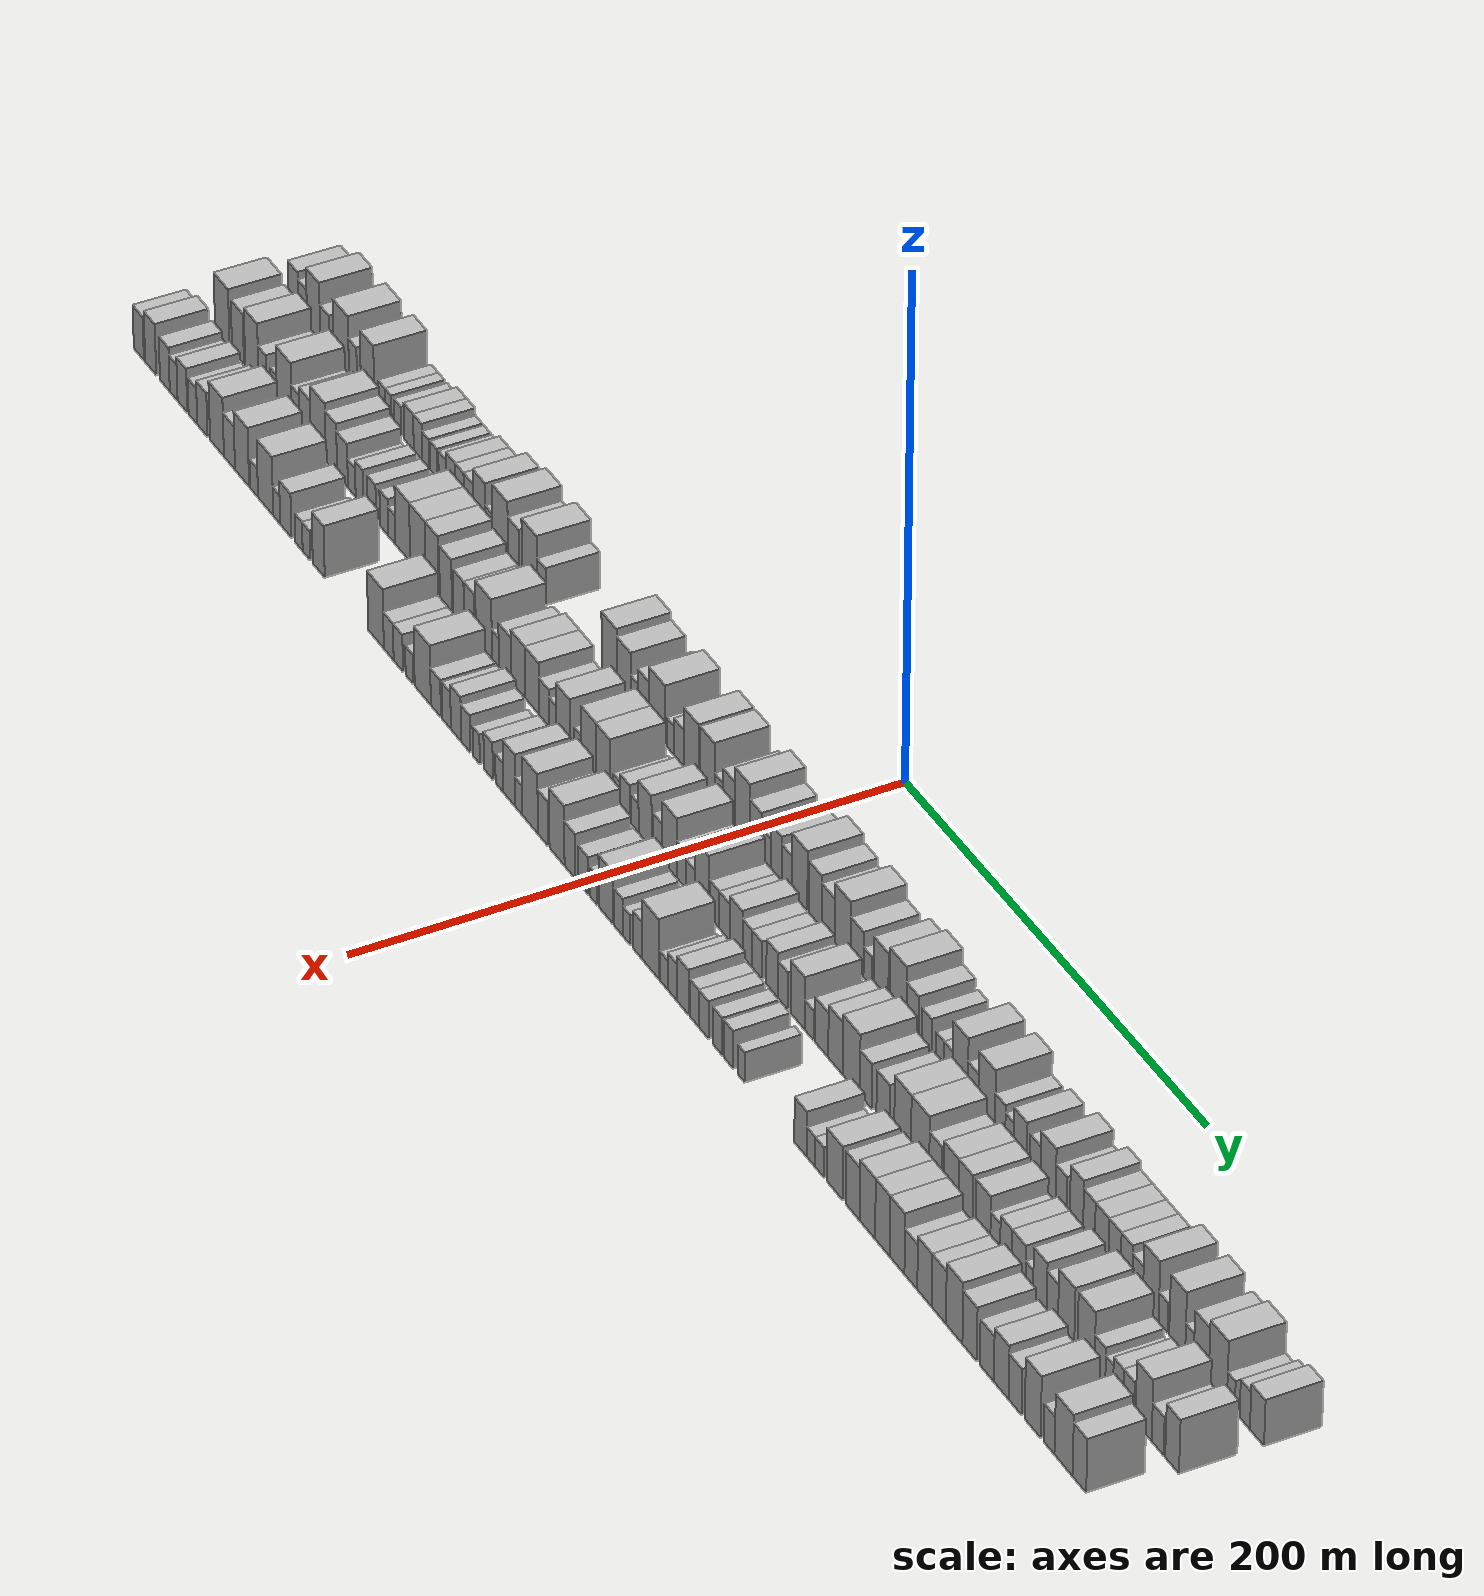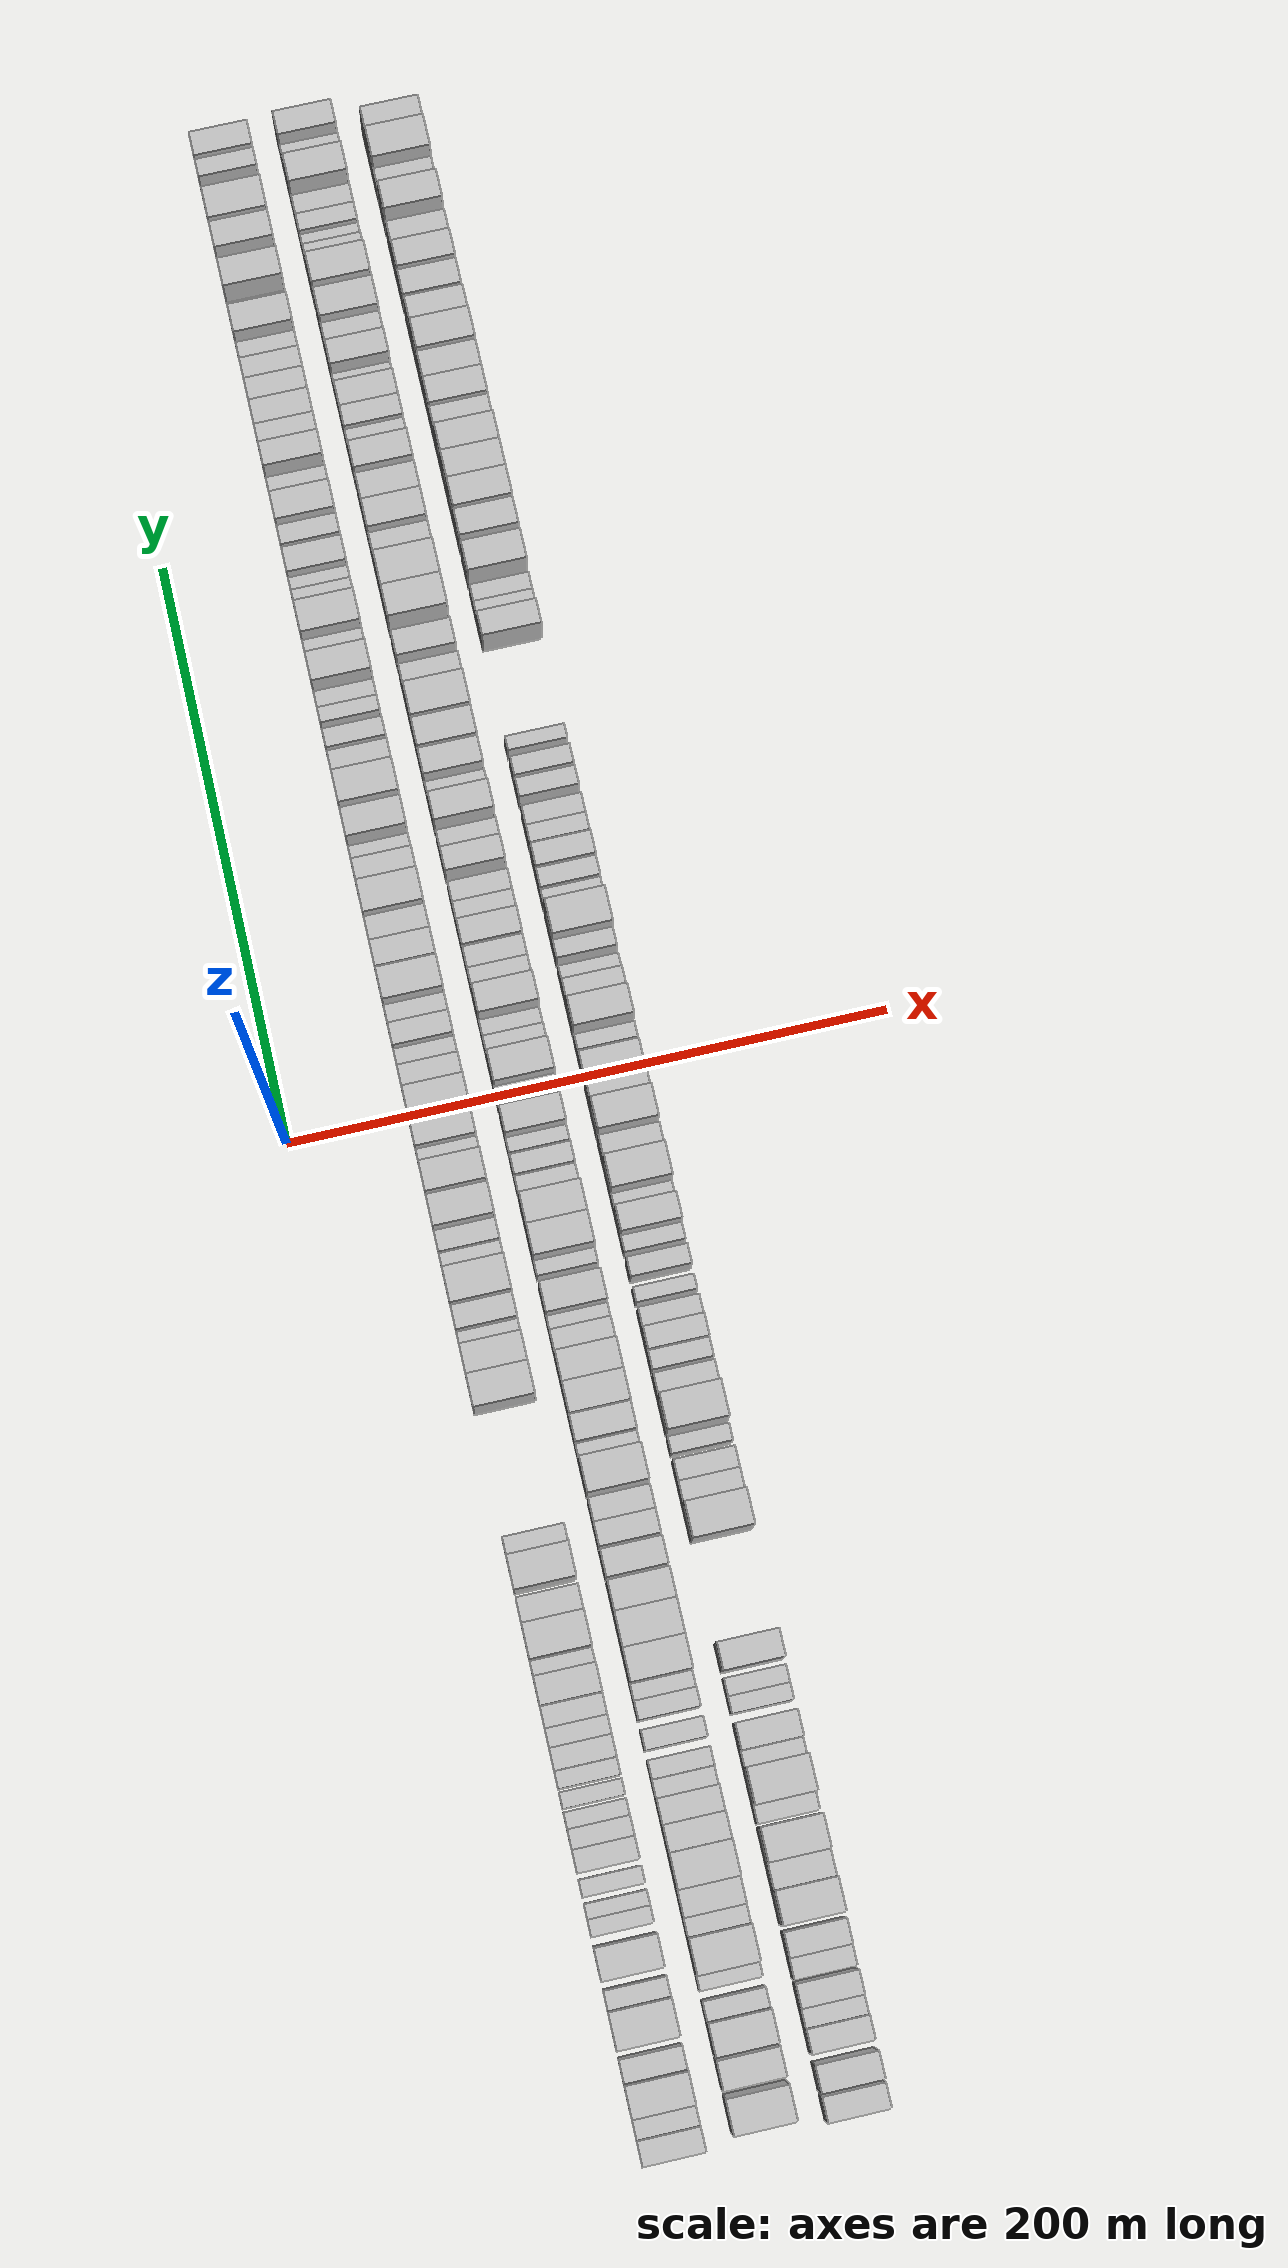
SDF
<sdf version="1.6">
 <world name="default">
  <scene>
   <sky><clouds><speed>12</speed></clouds></sky>
   <ambient>0.4 0.4 0.4 1</ambient>
   <background>0.7 0.7 0.7 1</background>
   <shadows>1</shadows>
  </scene>
  <gravity>0 0 -9.8066</gravity>
  <magnetic_field>6e-06 2.3e-05 -4.2e-05</magnetic_field>
  <physics default="0" name="default_physics" type="ode">
   <ode>
    <solver>
     <type>quick</type>
     <iters>10</iters>
     <sor>1.0</sor>
     <use_dynamic_moi_rescaling>0</use_dynamic_moi_rescaling>
    </solver>
    <constraints>
     <cfm>0</cfm>
     <erp>0.2</erp>
     <contact_max_correcting_vel>100</contact_max_correcting_vel>
     <contact_surface_layer>0.001</contact_surface_layer>
    </constraints>
   </ode>
   <max_step_size>0.004</max_step_size>
   <real_time_factor>1</real_time_factor>
   <real_time_update_rate>250</real_time_update_rate>
  </physics>
  <light name="sun" type="directional">
   <pose>0 0 10 0 0 0</pose>
   <diffuse>0.8 0.8 0.8 1</diffuse>
   <specular>0.2 0.2 0.2 1</specular>
   <attenuation>
    <range>1000</range>
    <constant>0.9</constant>
    <linear>0.01</linear>
    <quadratic>0.001</quadratic>
   </attenuation>
   <direction>-0.5 0.1 -0.9</direction>
  </light>
  <model name="building_1">
   <static>1</static>
   <pose>50.0000 -332.0885 0 0.000000 0.000000 0.000000</pose>
   <link name="link">
    <pose>0 0 9.00 0 0 0</pose>
    <collision name="collision"><geometry><box><size>20.0000 7.8230 18.0000</size></box></geometry></collision>
    <visual name="visual">
     <cast_shadows>0</cast_shadows>
     <geometry><box><size>20.0000 7.8230 18.0000</size></box></geometry>
     <material>
      <script>
       <uri>model://HANNAS_wall/materials/scripts</uri>
       <uri>model://HANNAS_wall/materials/textures</uri>
       <name>vrc/HANNAS_wall</name>
      </script>
     </material>
    </visual>
   </link>
  </model>
  <model name="building_2">
   <static>1</static>
   <pose>50.0000 -324.7958 0 0.000000 0.000000 0.000000</pose>
   <link name="link">
    <pose>0 0 7.50 0 0 0</pose>
    <collision name="collision"><geometry><box><size>20.0000 6.7623 15.0000</size></box></geometry></collision>
    <visual name="visual">
     <cast_shadows>0</cast_shadows>
     <geometry><box><size>20.0000 6.7623 15.0000</size></box></geometry>
     <material>
      <script>
       <uri>model://HANNAS_wall/materials/scripts</uri>
       <uri>model://HANNAS_wall/materials/textures</uri>
       <name>vrc/HANNAS_wall</name>
      </script>
     </material>
    </visual>
   </link>
  </model>
  <model name="building_3">
   <static>1</static>
   <pose>50.0000 -316.2842 0 0.000000 0.000000 0.000000</pose>
   <link name="link">
    <pose>0 0 12.00 0 0 0</pose>
    <collision name="collision"><geometry><box><size>20.0000 10.2610 24.0000</size></box></geometry></collision>
    <visual name="visual">
     <cast_shadows>0</cast_shadows>
     <geometry><box><size>20.0000 10.2610 24.0000</size></box></geometry>
     <material>
      <script>
       <uri>model://HANNAS_wall/materials/scripts</uri>
       <uri>model://HANNAS_wall/materials/textures</uri>
       <name>vrc/HANNAS_wall</name>
      </script>
     </material>
    </visual>
   </link>
  </model>
  <model name="building_4">
   <static>1</static>
   <pose>50.0000 -307.4432 0 0.000000 0.000000 0.000000</pose>
   <link name="link">
    <pose>0 0 7.50 0 0 0</pose>
    <collision name="collision"><geometry><box><size>20.0000 7.4209 15.0000</size></box></geometry></collision>
    <visual name="visual">
     <cast_shadows>0</cast_shadows>
     <geometry><box><size>20.0000 7.4209 15.0000</size></box></geometry>
     <material>
      <script>
       <uri>model://HANNAS_wall/materials/scripts</uri>
       <uri>model://HANNAS_wall/materials/textures</uri>
       <name>vrc/HANNAS_wall</name>
      </script>
     </material>
    </visual>
   </link>
  </model>
  <model name="building_5">
   <static>1</static>
   <pose>50.0000 -294.8028 0 0.000000 0.000000 0.000000</pose>
   <link name="link">
    <pose>0 0 12.00 0 0 0</pose>
    <collision name="collision"><geometry><box><size>20.0000 11.8599 24.0000</size></box></geometry></collision>
    <visual name="visual">
     <cast_shadows>0</cast_shadows>
     <geometry><box><size>20.0000 11.8599 24.0000</size></box></geometry>
     <material>
      <script>
       <uri>model://HANNAS_wall/materials/scripts</uri>
       <uri>model://HANNAS_wall/materials/textures</uri>
       <name>vrc/HANNAS_wall</name>
      </script>
     </material>
    </visual>
   </link>
  </model>
  <model name="building_6">
   <static>1</static>
   <pose>50.0000 -285.7504 0 0.000000 0.000000 0.000000</pose>
   <link name="link">
    <pose>0 0 7.50 0 0 0</pose>
    <collision name="collision"><geometry><box><size>20.0000 6.2450 15.0000</size></box></geometry></collision>
    <visual name="visual">
     <cast_shadows>0</cast_shadows>
     <geometry><box><size>20.0000 6.2450 15.0000</size></box></geometry>
     <material>
      <script>
       <uri>model://HANNAS_wall/materials/scripts</uri>
       <uri>model://HANNAS_wall/materials/textures</uri>
       <name>vrc/HANNAS_wall</name>
      </script>
     </material>
    </visual>
   </link>
  </model>
  <model name="building_7">
   <static>1</static>
   <pose>50.0000 -274.4512 0 0.000000 0.000000 0.000000</pose>
   <link name="link">
    <pose>0 0 12.00 0 0 0</pose>
    <collision name="collision"><geometry><box><size>20.0000 10.3534 24.0000</size></box></geometry></collision>
    <visual name="visual">
     <cast_shadows>0</cast_shadows>
     <geometry><box><size>20.0000 10.3534 24.0000</size></box></geometry>
     <material>
      <script>
       <uri>model://HANNAS_wall/materials/scripts</uri>
       <uri>model://HANNAS_wall/materials/textures</uri>
       <name>vrc/HANNAS_wall</name>
      </script>
     </material>
    </visual>
   </link>
  </model>
  <model name="building_8">
   <static>1</static>
   <pose>50.0000 -263.5391 0 0.000000 0.000000 0.000000</pose>
   <link name="link">
    <pose>0 0 6.00 0 0 0</pose>
    <collision name="collision"><geometry><box><size>20.0000 5.4707 12.0000</size></box></geometry></collision>
    <visual name="visual">
     <cast_shadows>0</cast_shadows>
     <geometry><box><size>20.0000 5.4707 12.0000</size></box></geometry>
     <material>
      <script>
       <uri>model://HANNAS_wall/materials/scripts</uri>
       <uri>model://HANNAS_wall/materials/textures</uri>
       <name>vrc/HANNAS_wall</name>
      </script>
     </material>
    </visual>
   </link>
  </model>
  <model name="building_9">
   <static>1</static>
   <pose>50.0000 -258.3980 0 0.000000 0.000000 0.000000</pose>
   <link name="link">
    <pose>0 0 6.00 0 0 0</pose>
    <collision name="collision"><geometry><box><size>20.0000 4.8115 12.0000</size></box></geometry></collision>
    <visual name="visual">
     <cast_shadows>0</cast_shadows>
     <geometry><box><size>20.0000 4.8115 12.0000</size></box></geometry>
     <material>
      <script>
       <uri>model://HANNAS_wall/materials/scripts</uri>
       <uri>model://HANNAS_wall/materials/textures</uri>
       <name>vrc/HANNAS_wall</name>
      </script>
     </material>
    </visual>
   </link>
  </model>
  <model name="building_10">
   <static>1</static>
   <pose>50.0000 -251.2447 0 0.000000 0.000000 0.000000</pose>
   <link name="link">
    <pose>0 0 6.00 0 0 0</pose>
    <collision name="collision"><geometry><box><size>20.0000 5.4951 12.0000</size></box></geometry></collision>
    <visual name="visual">
     <cast_shadows>0</cast_shadows>
     <geometry><box><size>20.0000 5.4951 12.0000</size></box></geometry>
     <material>
      <script>
       <uri>model://HANNAS_wall/materials/scripts</uri>
       <uri>model://HANNAS_wall/materials/textures</uri>
       <name>vrc/HANNAS_wall</name>
      </script>
     </material>
    </visual>
   </link>
  </model>
  <model name="building_11">
   <static>1</static>
   <pose>50.0000 -242.8179 0 0.000000 0.000000 0.000000</pose>
   <link name="link">
    <pose>0 0 7.50 0 0 0</pose>
    <collision name="collision"><geometry><box><size>20.0000 7.3586 15.0000</size></box></geometry></collision>
    <visual name="visual">
     <cast_shadows>0</cast_shadows>
     <geometry><box><size>20.0000 7.3586 15.0000</size></box></geometry>
     <material>
      <script>
       <uri>model://HANNAS_wall/materials/scripts</uri>
       <uri>model://HANNAS_wall/materials/textures</uri>
       <name>vrc/HANNAS_wall</name>
      </script>
     </material>
    </visual>
   </link>
  </model>
  <model name="building_12">
   <static>1</static>
   <pose>50.0000 -235.9339 0 0.000000 0.000000 0.000000</pose>
   <link name="link">
    <pose>0 0 7.50 0 0 0</pose>
    <collision name="collision"><geometry><box><size>20.0000 6.4093 15.0000</size></box></geometry></collision>
    <visual name="visual">
     <cast_shadows>0</cast_shadows>
     <geometry><box><size>20.0000 6.4093 15.0000</size></box></geometry>
     <material>
      <script>
       <uri>model://HANNAS_wall/materials/scripts</uri>
       <uri>model://HANNAS_wall/materials/textures</uri>
       <name>vrc/HANNAS_wall</name>
      </script>
     </material>
    </visual>
   </link>
  </model>
  <model name="building_13">
   <static>1</static>
   <pose>50.0000 -230.0838 0 0.000000 0.000000 0.000000</pose>
   <link name="link">
    <pose>0 0 6.00 0 0 0</pose>
    <collision name="collision"><geometry><box><size>20.0000 5.2909 12.0000</size></box></geometry></collision>
    <visual name="visual">
     <cast_shadows>0</cast_shadows>
     <geometry><box><size>20.0000 5.2909 12.0000</size></box></geometry>
     <material>
      <script>
       <uri>model://HANNAS_wall/materials/scripts</uri>
       <uri>model://HANNAS_wall/materials/textures</uri>
       <name>vrc/HANNAS_wall</name>
      </script>
     </material>
    </visual>
   </link>
  </model>
  <model name="building_14">
   <static>1</static>
   <pose>50.0000 -223.8202 0 0.000000 0.000000 0.000000</pose>
   <link name="link">
    <pose>0 0 6.00 0 0 0</pose>
    <collision name="collision"><geometry><box><size>20.0000 5.2363 12.0000</size></box></geometry></collision>
    <visual name="visual">
     <cast_shadows>0</cast_shadows>
     <geometry><box><size>20.0000 5.2363 12.0000</size></box></geometry>
     <material>
      <script>
       <uri>model://HANNAS_wall/materials/scripts</uri>
       <uri>model://HANNAS_wall/materials/textures</uri>
       <name>vrc/HANNAS_wall</name>
      </script>
     </material>
    </visual>
   </link>
  </model>
  <model name="building_15">
   <static>1</static>
   <pose>50.0000 -217.3628 0 0.000000 0.000000 0.000000</pose>
   <link name="link">
    <pose>0 0 6.00 0 0 0</pose>
    <collision name="collision"><geometry><box><size>20.0000 5.6786 12.0000</size></box></geometry></collision>
    <visual name="visual">
     <cast_shadows>0</cast_shadows>
     <geometry><box><size>20.0000 5.6786 12.0000</size></box></geometry>
     <material>
      <script>
       <uri>model://HANNAS_wall/materials/scripts</uri>
       <uri>model://HANNAS_wall/materials/textures</uri>
       <name>vrc/HANNAS_wall</name>
      </script>
     </material>
    </visual>
   </link>
  </model>
  <model name="building_16">
   <static>1</static>
   <pose>50.0000 -210.9133 0 0.000000 0.000000 0.000000</pose>
   <link name="link">
    <pose>0 0 7.50 0 0 0</pose>
    <collision name="collision"><geometry><box><size>20.0000 7.2203 15.0000</size></box></geometry></collision>
    <visual name="visual">
     <cast_shadows>0</cast_shadows>
     <geometry><box><size>20.0000 7.2203 15.0000</size></box></geometry>
     <material>
      <script>
       <uri>model://HANNAS_wall/materials/scripts</uri>
       <uri>model://HANNAS_wall/materials/textures</uri>
       <name>vrc/HANNAS_wall</name>
      </script>
     </material>
    </visual>
   </link>
  </model>
  <model name="building_17">
   <static>1</static>
   <pose>50.0000 -204.2345 0 0.000000 0.000000 0.000000</pose>
   <link name="link">
    <pose>0 0 7.50 0 0 0</pose>
    <collision name="collision"><geometry><box><size>20.0000 6.1373 15.0000</size></box></geometry></collision>
    <visual name="visual">
     <cast_shadows>0</cast_shadows>
     <geometry><box><size>20.0000 6.1373 15.0000</size></box></geometry>
     <material>
      <script>
       <uri>model://HANNAS_wall/materials/scripts</uri>
       <uri>model://HANNAS_wall/materials/textures</uri>
       <name>vrc/HANNAS_wall</name>
      </script>
     </material>
    </visual>
   </link>
  </model>
  <model name="building_18">
   <static>1</static>
   <pose>50.0000 -197.7044 0 0.000000 0.000000 0.000000</pose>
   <link name="link">
    <pose>0 0 7.50 0 0 0</pose>
    <collision name="collision"><geometry><box><size>20.0000 6.9229 15.0000</size></box></geometry></collision>
    <visual name="visual">
     <cast_shadows>0</cast_shadows>
     <geometry><box><size>20.0000 6.9229 15.0000</size></box></geometry>
     <material>
      <script>
       <uri>model://HANNAS_wall/materials/scripts</uri>
       <uri>model://HANNAS_wall/materials/textures</uri>
       <name>vrc/HANNAS_wall</name>
      </script>
     </material>
    </visual>
   </link>
  </model>
  <model name="building_19">
   <static>1</static>
   <pose>50.0000 -189.5532 0 0.000000 0.000000 0.000000</pose>
   <link name="link">
    <pose>0 0 10.50 0 0 0</pose>
    <collision name="collision"><geometry><box><size>20.0000 9.3796 21.0000</size></box></geometry></collision>
    <visual name="visual">
     <cast_shadows>0</cast_shadows>
     <geometry><box><size>20.0000 9.3796 21.0000</size></box></geometry>
     <material>
      <script>
       <uri>model://HANNAS_wall/materials/scripts</uri>
       <uri>model://HANNAS_wall/materials/textures</uri>
       <name>vrc/HANNAS_wall</name>
      </script>
     </material>
    </visual>
   </link>
  </model>
  <model name="building_20">
   <static>1</static>
   <pose>50.0000 -182.3100 0 0.000000 0.000000 0.000000</pose>
   <link name="link">
    <pose>0 0 6.00 0 0 0</pose>
    <collision name="collision"><geometry><box><size>20.0000 5.1069 12.0000</size></box></geometry></collision>
    <visual name="visual">
     <cast_shadows>0</cast_shadows>
     <geometry><box><size>20.0000 5.1069 12.0000</size></box></geometry>
     <material>
      <script>
       <uri>model://HANNAS_wall/materials/scripts</uri>
       <uri>model://HANNAS_wall/materials/textures</uri>
       <name>vrc/HANNAS_wall</name>
      </script>
     </material>
    </visual>
   </link>
  </model>
  <model name="building_21">
   <static>1</static>
   <pose>50.0000 -173.9936 0 0.000000 0.000000 0.000000</pose>
   <link name="link">
    <pose>0 0 12.00 0 0 0</pose>
    <collision name="collision"><geometry><box><size>20.0000 11.5259 24.0000</size></box></geometry></collision>
    <visual name="visual">
     <cast_shadows>0</cast_shadows>
     <geometry><box><size>20.0000 11.5259 24.0000</size></box></geometry>
     <material>
      <script>
       <uri>model://HANNAS_wall/materials/scripts</uri>
       <uri>model://HANNAS_wall/materials/textures</uri>
       <name>vrc/HANNAS_wall</name>
      </script>
     </material>
    </visual>
   </link>
  </model>
  <model name="building_22">
   <static>1</static>
   <pose>50.0000 -164.0392 0 0.000000 0.000000 0.000000</pose>
   <link name="link">
    <pose>0 0 9.00 0 0 0</pose>
    <collision name="collision"><geometry><box><size>20.0000 8.3828 18.0000</size></box></geometry></collision>
    <visual name="visual">
     <cast_shadows>0</cast_shadows>
     <geometry><box><size>20.0000 8.3828 18.0000</size></box></geometry>
     <material>
      <script>
       <uri>model://HANNAS_wall/materials/scripts</uri>
       <uri>model://HANNAS_wall/materials/textures</uri>
       <name>vrc/HANNAS_wall</name>
      </script>
     </material>
    </visual>
   </link>
  </model>
  <model name="building_23">
   <static>1</static>
   <pose>50.0000 -152.2214 0 0.000000 0.000000 0.000000</pose>
   <link name="link">
    <pose>0 0 12.00 0 0 0</pose>
    <collision name="collision"><geometry><box><size>20.0000 11.2528 24.0000</size></box></geometry></collision>
    <visual name="visual">
     <cast_shadows>0</cast_shadows>
     <geometry><box><size>20.0000 11.2528 24.0000</size></box></geometry>
     <material>
      <script>
       <uri>model://HANNAS_wall/materials/scripts</uri>
       <uri>model://HANNAS_wall/materials/textures</uri>
       <name>vrc/HANNAS_wall</name>
      </script>
     </material>
    </visual>
   </link>
  </model>
  <model name="building_24">
   <static>1</static>
   <pose>50.0000 -143.4578 0 0.000000 0.000000 0.000000</pose>
   <link name="link">
    <pose>0 0 7.50 0 0 0</pose>
    <collision name="collision"><geometry><box><size>20.0000 6.2745 15.0000</size></box></geometry></collision>
    <visual name="visual">
     <cast_shadows>0</cast_shadows>
     <geometry><box><size>20.0000 6.2745 15.0000</size></box></geometry>
     <material>
      <script>
       <uri>model://HANNAS_wall/materials/scripts</uri>
       <uri>model://HANNAS_wall/materials/textures</uri>
       <name>vrc/HANNAS_wall</name>
      </script>
     </material>
    </visual>
   </link>
  </model>
  <model name="building_25">
   <static>1</static>
   <pose>50.0000 -94.0179 0 0.000000 0.000000 0.000000</pose>
   <link name="link">
    <pose>0 0 12.00 0 0 0</pose>
    <collision name="collision"><geometry><box><size>20.0000 10.8684 24.0000</size></box></geometry></collision>
    <visual name="visual">
     <cast_shadows>0</cast_shadows>
     <geometry><box><size>20.0000 10.8684 24.0000</size></box></geometry>
     <material>
      <script>
       <uri>model://HANNAS_wall/materials/scripts</uri>
       <uri>model://HANNAS_wall/materials/textures</uri>
       <name>vrc/HANNAS_wall</name>
      </script>
     </material>
    </visual>
   </link>
  </model>
  <model name="building_26">
   <static>1</static>
   <pose>50.0000 -83.5271 0 0.000000 0.000000 0.000000</pose>
   <link name="link">
    <pose>0 0 10.50 0 0 0</pose>
    <collision name="collision"><geometry><box><size>20.0000 10.1133 21.0000</size></box></geometry></collision>
    <visual name="visual">
     <cast_shadows>0</cast_shadows>
     <geometry><box><size>20.0000 10.1133 21.0000</size></box></geometry>
     <material>
      <script>
       <uri>model://HANNAS_wall/materials/scripts</uri>
       <uri>model://HANNAS_wall/materials/textures</uri>
       <name>vrc/HANNAS_wall</name>
      </script>
     </material>
    </visual>
   </link>
  </model>
  <model name="building_27">
   <static>1</static>
   <pose>50.0000 -75.9997 0 0.000000 0.000000 0.000000</pose>
   <link name="link">
    <pose>0 0 6.00 0 0 0</pose>
    <collision name="collision"><geometry><box><size>20.0000 4.9413 12.0000</size></box></geometry></collision>
    <visual name="visual">
     <cast_shadows>0</cast_shadows>
     <geometry><box><size>20.0000 4.9413 12.0000</size></box></geometry>
     <material>
      <script>
       <uri>model://HANNAS_wall/materials/scripts</uri>
       <uri>model://HANNAS_wall/materials/textures</uri>
       <name>vrc/HANNAS_wall</name>
      </script>
     </material>
    </visual>
   </link>
  </model>
  <model name="building_28">
   <static>1</static>
   <pose>50.0000 -69.5261 0 0.000000 0.000000 0.000000</pose>
   <link name="link">
    <pose>0 0 9.00 0 0 0</pose>
    <collision name="collision"><geometry><box><size>20.0000 8.0060 18.0000</size></box></geometry></collision>
    <visual name="visual">
     <cast_shadows>0</cast_shadows>
     <geometry><box><size>20.0000 8.0060 18.0000</size></box></geometry>
     <material>
      <script>
       <uri>model://HANNAS_wall/materials/scripts</uri>
       <uri>model://HANNAS_wall/materials/textures</uri>
       <name>vrc/HANNAS_wall</name>
      </script>
     </material>
    </visual>
   </link>
  </model>
  <model name="building_29">
   <static>1</static>
   <pose>50.0000 -59.6290 0 0.000000 0.000000 0.000000</pose>
   <link name="link">
    <pose>0 0 12.00 0 0 0</pose>
    <collision name="collision"><geometry><box><size>20.0000 11.7882 24.0000</size></box></geometry></collision>
    <visual name="visual">
     <cast_shadows>0</cast_shadows>
     <geometry><box><size>20.0000 11.7882 24.0000</size></box></geometry>
     <material>
      <script>
       <uri>model://HANNAS_wall/materials/scripts</uri>
       <uri>model://HANNAS_wall/materials/textures</uri>
       <name>vrc/HANNAS_wall</name>
      </script>
     </material>
    </visual>
   </link>
  </model>
  <model name="building_30">
   <static>1</static>
   <pose>50.0000 -50.1705 0 0.000000 0.000000 0.000000</pose>
   <link name="link">
    <pose>0 0 6.00 0 0 0</pose>
    <collision name="collision"><geometry><box><size>20.0000 5.1288 12.0000</size></box></geometry></collision>
    <visual name="visual">
     <cast_shadows>0</cast_shadows>
     <geometry><box><size>20.0000 5.1288 12.0000</size></box></geometry>
     <material>
      <script>
       <uri>model://HANNAS_wall/materials/scripts</uri>
       <uri>model://HANNAS_wall/materials/textures</uri>
       <name>vrc/HANNAS_wall</name>
      </script>
     </material>
    </visual>
   </link>
  </model>
  <model name="building_31">
   <static>1</static>
   <pose>50.0000 -44.0723 0 0.000000 0.000000 0.000000</pose>
   <link name="link">
    <pose>0 0 7.50 0 0 0</pose>
    <collision name="collision"><geometry><box><size>20.0000 7.0677 15.0000</size></box></geometry></collision>
    <visual name="visual">
     <cast_shadows>0</cast_shadows>
     <geometry><box><size>20.0000 7.0677 15.0000</size></box></geometry>
     <material>
      <script>
       <uri>model://HANNAS_wall/materials/scripts</uri>
       <uri>model://HANNAS_wall/materials/textures</uri>
       <name>vrc/HANNAS_wall</name>
      </script>
     </material>
    </visual>
   </link>
  </model>
  <model name="building_32">
   <static>1</static>
   <pose>50.0000 -35.3034 0 0.000000 0.000000 0.000000</pose>
   <link name="link">
    <pose>0 0 12.00 0 0 0</pose>
    <collision name="collision"><geometry><box><size>20.0000 10.4701 24.0000</size></box></geometry></collision>
    <visual name="visual">
     <cast_shadows>0</cast_shadows>
     <geometry><box><size>20.0000 10.4701 24.0000</size></box></geometry>
     <material>
      <script>
       <uri>model://HANNAS_wall/materials/scripts</uri>
       <uri>model://HANNAS_wall/materials/textures</uri>
       <name>vrc/HANNAS_wall</name>
      </script>
     </material>
    </visual>
   </link>
  </model>
  <model name="building_33">
   <static>1</static>
   <pose>50.0000 -23.9722 0 0.000000 0.000000 0.000000</pose>
   <link name="link">
    <pose>0 0 12.00 0 0 0</pose>
    <collision name="collision"><geometry><box><size>20.0000 10.1921 24.0000</size></box></geometry></collision>
    <visual name="visual">
     <cast_shadows>0</cast_shadows>
     <geometry><box><size>20.0000 10.1921 24.0000</size></box></geometry>
     <material>
      <script>
       <uri>model://HANNAS_wall/materials/scripts</uri>
       <uri>model://HANNAS_wall/materials/textures</uri>
       <name>vrc/HANNAS_wall</name>
      </script>
     </material>
    </visual>
   </link>
  </model>
  <model name="building_34">
   <static>1</static>
   <pose>50.0000 -15.9255 0 0.000000 0.000000 0.000000</pose>
   <link name="link">
    <pose>0 0 6.00 0 0 0</pose>
    <collision name="collision"><geometry><box><size>20.0000 5.9014 12.0000</size></box></geometry></collision>
    <visual name="visual">
     <cast_shadows>0</cast_shadows>
     <geometry><box><size>20.0000 5.9014 12.0000</size></box></geometry>
     <material>
      <script>
       <uri>model://HANNAS_wall/materials/scripts</uri>
       <uri>model://HANNAS_wall/materials/textures</uri>
       <name>vrc/HANNAS_wall</name>
      </script>
     </material>
    </visual>
   </link>
  </model>
  <model name="building_35">
   <static>1</static>
   <pose>50.0000 -8.6745 0 0.000000 0.000000 0.000000</pose>
   <link name="link">
    <pose>0 0 9.00 0 0 0</pose>
    <collision name="collision"><geometry><box><size>20.0000 8.6005 18.0000</size></box></geometry></collision>
    <visual name="visual">
     <cast_shadows>0</cast_shadows>
     <geometry><box><size>20.0000 8.6005 18.0000</size></box></geometry>
     <material>
      <script>
       <uri>model://HANNAS_wall/materials/scripts</uri>
       <uri>model://HANNAS_wall/materials/textures</uri>
       <name>vrc/HANNAS_wall</name>
      </script>
     </material>
    </visual>
   </link>
  </model>
  <model name="building_36">
   <static>1</static>
   <pose>50.0000 0.7981 0 0.000000 0.000000 0.000000</pose>
   <link name="link">
    <pose>0 0 12.00 0 0 0</pose>
    <collision name="collision"><geometry><box><size>20.0000 10.3448 24.0000</size></box></geometry></collision>
    <visual name="visual">
     <cast_shadows>0</cast_shadows>
     <geometry><box><size>20.0000 10.3448 24.0000</size></box></geometry>
     <material>
      <script>
       <uri>model://HANNAS_wall/materials/scripts</uri>
       <uri>model://HANNAS_wall/materials/textures</uri>
       <name>vrc/HANNAS_wall</name>
      </script>
     </material>
    </visual>
   </link>
  </model>
  <model name="building_37">
   <static>1</static>
   <pose>50.0000 10.0276 0 0.000000 0.000000 0.000000</pose>
   <link name="link">
    <pose>0 0 9.00 0 0 0</pose>
    <collision name="collision"><geometry><box><size>20.0000 8.1141 18.0000</size></box></geometry></collision>
    <visual name="visual">
     <cast_shadows>0</cast_shadows>
     <geometry><box><size>20.0000 8.1141 18.0000</size></box></geometry>
     <material>
      <script>
       <uri>model://HANNAS_wall/materials/scripts</uri>
       <uri>model://HANNAS_wall/materials/textures</uri>
       <name>vrc/HANNAS_wall</name>
      </script>
     </material>
    </visual>
   </link>
  </model>
  <model name="building_38">
   <static>1</static>
   <pose>50.0000 17.8904 0 0.000000 0.000000 0.000000</pose>
   <link name="link">
    <pose>0 0 6.00 0 0 0</pose>
    <collision name="collision"><geometry><box><size>20.0000 5.6115 12.0000</size></box></geometry></collision>
    <visual name="visual">
     <cast_shadows>0</cast_shadows>
     <geometry><box><size>20.0000 5.6115 12.0000</size></box></geometry>
     <material>
      <script>
       <uri>model://HANNAS_wall/materials/scripts</uri>
       <uri>model://HANNAS_wall/materials/textures</uri>
       <name>vrc/HANNAS_wall</name>
      </script>
     </material>
    </visual>
   </link>
  </model>
  <model name="building_39">
   <static>1</static>
   <pose>50.0000 24.4787 0 0.000000 0.000000 0.000000</pose>
   <link name="link">
    <pose>0 0 9.00 0 0 0</pose>
    <collision name="collision"><geometry><box><size>20.0000 7.5652 18.0000</size></box></geometry></collision>
    <visual name="visual">
     <cast_shadows>0</cast_shadows>
     <geometry><box><size>20.0000 7.5652 18.0000</size></box></geometry>
     <material>
      <script>
       <uri>model://HANNAS_wall/materials/scripts</uri>
       <uri>model://HANNAS_wall/materials/textures</uri>
       <name>vrc/HANNAS_wall</name>
      </script>
     </material>
    </visual>
   </link>
  </model>
  <model name="building_40">
   <static>1</static>
   <pose>50.0000 31.5845 0 0.000000 0.000000 0.000000</pose>
   <link name="link">
    <pose>0 0 7.50 0 0 0</pose>
    <collision name="collision"><geometry><box><size>20.0000 6.6463 15.0000</size></box></geometry></collision>
    <visual name="visual">
     <cast_shadows>0</cast_shadows>
     <geometry><box><size>20.0000 6.6463 15.0000</size></box></geometry>
     <material>
      <script>
       <uri>model://HANNAS_wall/materials/scripts</uri>
       <uri>model://HANNAS_wall/materials/textures</uri>
       <name>vrc/HANNAS_wall</name>
      </script>
     </material>
    </visual>
   </link>
  </model>
  <model name="building_41">
   <static>1</static>
   <pose>50.0000 40.3000 0 0.000000 0.000000 0.000000</pose>
   <link name="link">
    <pose>0 0 12.00 0 0 0</pose>
    <collision name="collision"><geometry><box><size>20.0000 10.7847 24.0000</size></box></geometry></collision>
    <visual name="visual">
     <cast_shadows>0</cast_shadows>
     <geometry><box><size>20.0000 10.7847 24.0000</size></box></geometry>
     <material>
      <script>
       <uri>model://HANNAS_wall/materials/scripts</uri>
       <uri>model://HANNAS_wall/materials/textures</uri>
       <name>vrc/HANNAS_wall</name>
      </script>
     </material>
    </visual>
   </link>
  </model>
  <model name="building_42">
   <static>1</static>
   <pose>50.0000 51.1295 0 0.000000 0.000000 0.000000</pose>
   <link name="link">
    <pose>0 0 10.50 0 0 0</pose>
    <collision name="collision"><geometry><box><size>20.0000 8.8744 21.0000</size></box></geometry></collision>
    <visual name="visual">
     <cast_shadows>0</cast_shadows>
     <geometry><box><size>20.0000 8.8744 21.0000</size></box></geometry>
     <material>
      <script>
       <uri>model://HANNAS_wall/materials/scripts</uri>
       <uri>model://HANNAS_wall/materials/textures</uri>
       <name>vrc/HANNAS_wall</name>
      </script>
     </material>
    </visual>
   </link>
  </model>
  <model name="building_43">
   <static>1</static>
   <pose>50.0000 59.9366 0 0.000000 0.000000 0.000000</pose>
   <link name="link">
    <pose>0 0 9.00 0 0 0</pose>
    <collision name="collision"><geometry><box><size>20.0000 8.7396 18.0000</size></box></geometry></collision>
    <visual name="visual">
     <cast_shadows>0</cast_shadows>
     <geometry><box><size>20.0000 8.7396 18.0000</size></box></geometry>
     <material>
      <script>
       <uri>model://HANNAS_wall/materials/scripts</uri>
       <uri>model://HANNAS_wall/materials/textures</uri>
       <name>vrc/HANNAS_wall</name>
      </script>
     </material>
    </visual>
   </link>
  </model>
  <model name="building_44">
   <static>1</static>
   <pose>50.0000 69.8404 0 0.000000 0.000000 0.000000</pose>
   <link name="link">
    <pose>0 0 12.00 0 0 0</pose>
    <collision name="collision"><geometry><box><size>20.0000 11.0680 24.0000</size></box></geometry></collision>
    <visual name="visual">
     <cast_shadows>0</cast_shadows>
     <geometry><box><size>20.0000 11.0680 24.0000</size></box></geometry>
     <material>
      <script>
       <uri>model://HANNAS_wall/materials/scripts</uri>
       <uri>model://HANNAS_wall/materials/textures</uri>
       <name>vrc/HANNAS_wall</name>
      </script>
     </material>
    </visual>
   </link>
  </model>
  <model name="building_45">
   <static>1</static>
   <pose>50.0000 79.7272 0 0.000000 0.000000 0.000000</pose>
   <link name="link">
    <pose>0 0 9.00 0 0 0</pose>
    <collision name="collision"><geometry><box><size>20.0000 8.7056 18.0000</size></box></geometry></collision>
    <visual name="visual">
     <cast_shadows>0</cast_shadows>
     <geometry><box><size>20.0000 8.7056 18.0000</size></box></geometry>
     <material>
      <script>
       <uri>model://HANNAS_wall/materials/scripts</uri>
       <uri>model://HANNAS_wall/materials/textures</uri>
       <name>vrc/HANNAS_wall</name>
      </script>
     </material>
    </visual>
   </link>
  </model>
  <model name="building_46">
   <static>1</static>
   <pose>50.0000 87.0113 0 0.000000 0.000000 0.000000</pose>
   <link name="link">
    <pose>0 0 6.00 0 0 0</pose>
    <collision name="collision"><geometry><box><size>20.0000 5.8626 12.0000</size></box></geometry></collision>
    <visual name="visual">
     <cast_shadows>0</cast_shadows>
     <geometry><box><size>20.0000 5.8626 12.0000</size></box></geometry>
     <material>
      <script>
       <uri>model://HANNAS_wall/materials/scripts</uri>
       <uri>model://HANNAS_wall/materials/textures</uri>
       <name>vrc/HANNAS_wall</name>
      </script>
     </material>
    </visual>
   </link>
  </model>
  <model name="building_47">
   <static>1</static>
   <pose>50.0000 95.8644 0 0.000000 0.000000 0.000000</pose>
   <link name="link">
    <pose>0 0 10.50 0 0 0</pose>
    <collision name="collision"><geometry><box><size>20.0000 9.8436 21.0000</size></box></geometry></collision>
    <visual name="visual">
     <cast_shadows>0</cast_shadows>
     <geometry><box><size>20.0000 9.8436 21.0000</size></box></geometry>
     <material>
      <script>
       <uri>model://HANNAS_wall/materials/scripts</uri>
       <uri>model://HANNAS_wall/materials/textures</uri>
       <name>vrc/HANNAS_wall</name>
      </script>
     </material>
    </visual>
   </link>
  </model>
  <model name="building_48">
   <static>1</static>
   <pose>50.0000 107.3642 0 0.000000 0.000000 0.000000</pose>
   <link name="link">
    <pose>0 0 12.00 0 0 0</pose>
    <collision name="collision"><geometry><box><size>20.0000 11.1561 24.0000</size></box></geometry></collision>
    <visual name="visual">
     <cast_shadows>0</cast_shadows>
     <geometry><box><size>20.0000 11.1561 24.0000</size></box></geometry>
     <material>
      <script>
       <uri>model://HANNAS_wall/materials/scripts</uri>
       <uri>model://HANNAS_wall/materials/textures</uri>
       <name>vrc/HANNAS_wall</name>
      </script>
     </material>
    </visual>
   </link>
  </model>
  <model name="building_49">
   <static>1</static>
   <pose>50.0000 117.0951 0 0.000000 0.000000 0.000000</pose>
   <link name="link">
    <pose>0 0 9.00 0 0 0</pose>
    <collision name="collision"><geometry><box><size>20.0000 8.3057 18.0000</size></box></geometry></collision>
    <visual name="visual">
     <cast_shadows>0</cast_shadows>
     <geometry><box><size>20.0000 8.3057 18.0000</size></box></geometry>
     <material>
      <script>
       <uri>model://HANNAS_wall/materials/scripts</uri>
       <uri>model://HANNAS_wall/materials/textures</uri>
       <name>vrc/HANNAS_wall</name>
      </script>
     </material>
    </visual>
   </link>
  </model>
  <model name="building_50">
   <static>1</static>
   <pose>50.0000 126.5278 0 0.000000 0.000000 0.000000</pose>
   <link name="link">
    <pose>0 0 7.50 0 0 0</pose>
    <collision name="collision"><geometry><box><size>20.0000 6.5597 15.0000</size></box></geometry></collision>
    <visual name="visual">
     <cast_shadows>0</cast_shadows>
     <geometry><box><size>20.0000 6.5597 15.0000</size></box></geometry>
     <material>
      <script>
       <uri>model://HANNAS_wall/materials/scripts</uri>
       <uri>model://HANNAS_wall/materials/textures</uri>
       <name>vrc/HANNAS_wall</name>
      </script>
     </material>
    </visual>
   </link>
  </model>
  <model name="building_51">
   <static>1</static>
   <pose>50.0000 135.4834 0 0.000000 0.000000 0.000000</pose>
   <link name="link">
    <pose>0 0 6.00 0 0 0</pose>
    <collision name="collision"><geometry><box><size>20.0000 5.3515 12.0000</size></box></geometry></collision>
    <visual name="visual">
     <cast_shadows>0</cast_shadows>
     <geometry><box><size>20.0000 5.3515 12.0000</size></box></geometry>
     <material>
      <script>
       <uri>model://HANNAS_wall/materials/scripts</uri>
       <uri>model://HANNAS_wall/materials/textures</uri>
       <name>vrc/HANNAS_wall</name>
      </script>
     </material>
    </visual>
   </link>
  </model>
  <model name="building_52">
   <static>1</static>
   <pose>50.0000 140.9551 0 0.000000 0.000000 0.000000</pose>
   <link name="link">
    <pose>0 0 6.00 0 0 0</pose>
    <collision name="collision"><geometry><box><size>20.0000 5.5919 12.0000</size></box></geometry></collision>
    <visual name="visual">
     <cast_shadows>0</cast_shadows>
     <geometry><box><size>20.0000 5.5919 12.0000</size></box></geometry>
     <material>
      <script>
       <uri>model://HANNAS_wall/materials/scripts</uri>
       <uri>model://HANNAS_wall/materials/textures</uri>
       <name>vrc/HANNAS_wall</name>
      </script>
     </material>
    </visual>
   </link>
  </model>
  <model name="building_53">
   <static>1</static>
   <pose>50.0000 148.7981 0 0.000000 0.000000 0.000000</pose>
   <link name="link">
    <pose>0 0 12.00 0 0 0</pose>
    <collision name="collision"><geometry><box><size>20.0000 10.0943 24.0000</size></box></geometry></collision>
    <visual name="visual">
     <cast_shadows>0</cast_shadows>
     <geometry><box><size>20.0000 10.0943 24.0000</size></box></geometry>
     <material>
      <script>
       <uri>model://HANNAS_wall/materials/scripts</uri>
       <uri>model://HANNAS_wall/materials/textures</uri>
       <name>vrc/HANNAS_wall</name>
      </script>
     </material>
    </visual>
   </link>
  </model>
  <model name="building_54">
   <static>1</static>
   <pose>50.0000 157.2991 0 0.000000 0.000000 0.000000</pose>
   <link name="link">
    <pose>0 0 7.50 0 0 0</pose>
    <collision name="collision"><geometry><box><size>20.0000 6.9077 15.0000</size></box></geometry></collision>
    <visual name="visual">
     <cast_shadows>0</cast_shadows>
     <geometry><box><size>20.0000 6.9077 15.0000</size></box></geometry>
     <material>
      <script>
       <uri>model://HANNAS_wall/materials/scripts</uri>
       <uri>model://HANNAS_wall/materials/textures</uri>
       <name>vrc/HANNAS_wall</name>
      </script>
     </material>
    </visual>
   </link>
  </model>
  <model name="building_55">
   <static>1</static>
   <pose>50.0000 166.2611 0 0.000000 0.000000 0.000000</pose>
   <link name="link">
    <pose>0 0 12.00 0 0 0</pose>
    <collision name="collision"><geometry><box><size>20.0000 11.0164 24.0000</size></box></geometry></collision>
    <visual name="visual">
     <cast_shadows>0</cast_shadows>
     <geometry><box><size>20.0000 11.0164 24.0000</size></box></geometry>
     <material>
      <script>
       <uri>model://HANNAS_wall/materials/scripts</uri>
       <uri>model://HANNAS_wall/materials/textures</uri>
       <name>vrc/HANNAS_wall</name>
      </script>
     </material>
    </visual>
   </link>
  </model>
  <model name="building_56">
   <static>1</static>
   <pose>50.0000 175.1466 0 0.000000 0.000000 0.000000</pose>
   <link name="link">
    <pose>0 0 7.50 0 0 0</pose>
    <collision name="collision"><geometry><box><size>20.0000 6.7548 15.0000</size></box></geometry></collision>
    <visual name="visual">
     <cast_shadows>0</cast_shadows>
     <geometry><box><size>20.0000 6.7548 15.0000</size></box></geometry>
     <material>
      <script>
       <uri>model://HANNAS_wall/materials/scripts</uri>
       <uri>model://HANNAS_wall/materials/textures</uri>
       <name>vrc/HANNAS_wall</name>
      </script>
     </material>
    </visual>
   </link>
  </model>
  <model name="building_57">
   <static>1</static>
   <pose>50.0000 181.1910 0 0.000000 0.000000 0.000000</pose>
   <link name="link">
    <pose>0 0 6.00 0 0 0</pose>
    <collision name="collision"><geometry><box><size>20.0000 5.3339 12.0000</size></box></geometry></collision>
    <visual name="visual">
     <cast_shadows>0</cast_shadows>
     <geometry><box><size>20.0000 5.3339 12.0000</size></box></geometry>
     <material>
      <script>
       <uri>model://HANNAS_wall/materials/scripts</uri>
       <uri>model://HANNAS_wall/materials/textures</uri>
       <name>vrc/HANNAS_wall</name>
      </script>
     </material>
    </visual>
   </link>
  </model>
  <model name="building_58">
   <static>1</static>
   <pose>50.0000 188.2223 0 0.000000 0.000000 0.000000</pose>
   <link name="link">
    <pose>0 0 9.00 0 0 0</pose>
    <collision name="collision"><geometry><box><size>20.0000 8.7287 18.0000</size></box></geometry></collision>
    <visual name="visual">
     <cast_shadows>0</cast_shadows>
     <geometry><box><size>20.0000 8.7287 18.0000</size></box></geometry>
     <material>
      <script>
       <uri>model://HANNAS_wall/materials/scripts</uri>
       <uri>model://HANNAS_wall/materials/textures</uri>
       <name>vrc/HANNAS_wall</name>
      </script>
     </material>
    </visual>
   </link>
  </model>
  <model name="building_59">
   <static>1</static>
   <pose>50.0000 198.0226 0 0.000000 0.000000 0.000000</pose>
   <link name="link">
    <pose>0 0 7.50 0 0 0</pose>
    <collision name="collision"><geometry><box><size>20.0000 6.8718 15.0000</size></box></geometry></collision>
    <visual name="visual">
     <cast_shadows>0</cast_shadows>
     <geometry><box><size>20.0000 6.8718 15.0000</size></box></geometry>
     <material>
      <script>
       <uri>model://HANNAS_wall/materials/scripts</uri>
       <uri>model://HANNAS_wall/materials/textures</uri>
       <name>vrc/HANNAS_wall</name>
      </script>
     </material>
    </visual>
   </link>
  </model>
  <model name="building_60">
   <static>1</static>
   <pose>50.0000 206.3866 0 0.000000 0.000000 0.000000</pose>
   <link name="link">
    <pose>0 0 10.50 0 0 0</pose>
    <collision name="collision"><geometry><box><size>20.0000 9.8563 21.0000</size></box></geometry></collision>
    <visual name="visual">
     <cast_shadows>0</cast_shadows>
     <geometry><box><size>20.0000 9.8563 21.0000</size></box></geometry>
     <material>
      <script>
       <uri>model://HANNAS_wall/materials/scripts</uri>
       <uri>model://HANNAS_wall/materials/textures</uri>
       <name>vrc/HANNAS_wall</name>
      </script>
     </material>
    </visual>
   </link>
  </model>
  <model name="building_61">
   <static>1</static>
   <pose>50.0000 214.8966 0 0.000000 0.000000 0.000000</pose>
   <link name="link">
    <pose>0 0 7.50 0 0 0</pose>
    <collision name="collision"><geometry><box><size>20.0000 7.1636 15.0000</size></box></geometry></collision>
    <visual name="visual">
     <cast_shadows>0</cast_shadows>
     <geometry><box><size>20.0000 7.1636 15.0000</size></box></geometry>
     <material>
      <script>
       <uri>model://HANNAS_wall/materials/scripts</uri>
       <uri>model://HANNAS_wall/materials/textures</uri>
       <name>vrc/HANNAS_wall</name>
      </script>
     </material>
    </visual>
   </link>
  </model>
  <model name="building_62">
   <static>1</static>
   <pose>50.0000 224.7553 0 0.000000 0.000000 0.000000</pose>
   <link name="link">
    <pose>0 0 10.50 0 0 0</pose>
    <collision name="collision"><geometry><box><size>20.0000 8.5537 21.0000</size></box></geometry></collision>
    <visual name="visual">
     <cast_shadows>0</cast_shadows>
     <geometry><box><size>20.0000 8.5537 21.0000</size></box></geometry>
     <material>
      <script>
       <uri>model://HANNAS_wall/materials/scripts</uri>
       <uri>model://HANNAS_wall/materials/textures</uri>
       <name>vrc/HANNAS_wall</name>
      </script>
     </material>
    </visual>
   </link>
  </model>
  <model name="building_63">
   <static>1</static>
   <pose>50.0000 232.7942 0 0.000000 0.000000 0.000000</pose>
   <link name="link">
    <pose>0 0 9.00 0 0 0</pose>
    <collision name="collision"><geometry><box><size>20.0000 7.5243 18.0000</size></box></geometry></collision>
    <visual name="visual">
     <cast_shadows>0</cast_shadows>
     <geometry><box><size>20.0000 7.5243 18.0000</size></box></geometry>
     <material>
      <script>
       <uri>model://HANNAS_wall/materials/scripts</uri>
       <uri>model://HANNAS_wall/materials/textures</uri>
       <name>vrc/HANNAS_wall</name>
      </script>
     </material>
    </visual>
   </link>
  </model>
  <model name="building_64">
   <static>1</static>
   <pose>50.0000 240.9045 0 0.000000 0.000000 0.000000</pose>
   <link name="link">
    <pose>0 0 9.00 0 0 0</pose>
    <collision name="collision"><geometry><box><size>20.0000 8.6962 18.0000</size></box></geometry></collision>
    <visual name="visual">
     <cast_shadows>0</cast_shadows>
     <geometry><box><size>20.0000 8.6962 18.0000</size></box></geometry>
     <material>
      <script>
       <uri>model://HANNAS_wall/materials/scripts</uri>
       <uri>model://HANNAS_wall/materials/textures</uri>
       <name>vrc/HANNAS_wall</name>
      </script>
     </material>
    </visual>
   </link>
  </model>
  <model name="building_65">
   <static>1</static>
   <pose>50.0000 249.1445 0 0.000000 0.000000 0.000000</pose>
   <link name="link">
    <pose>0 0 9.00 0 0 0</pose>
    <collision name="collision"><geometry><box><size>20.0000 7.7839 18.0000</size></box></geometry></collision>
    <visual name="visual">
     <cast_shadows>0</cast_shadows>
     <geometry><box><size>20.0000 7.7839 18.0000</size></box></geometry>
     <material>
      <script>
       <uri>model://HANNAS_wall/materials/scripts</uri>
       <uri>model://HANNAS_wall/materials/textures</uri>
       <name>vrc/HANNAS_wall</name>
      </script>
     </material>
    </visual>
   </link>
  </model>
  <model name="building_66">
   <static>1</static>
   <pose>50.0000 256.6748 0 0.000000 0.000000 0.000000</pose>
   <link name="link">
    <pose>0 0 9.00 0 0 0</pose>
    <collision name="collision"><geometry><box><size>20.0000 7.2768 18.0000</size></box></geometry></collision>
    <visual name="visual">
     <cast_shadows>0</cast_shadows>
     <geometry><box><size>20.0000 7.2768 18.0000</size></box></geometry>
     <material>
      <script>
       <uri>model://HANNAS_wall/materials/scripts</uri>
       <uri>model://HANNAS_wall/materials/textures</uri>
       <name>vrc/HANNAS_wall</name>
      </script>
     </material>
    </visual>
   </link>
  </model>
  <model name="building_67">
   <static>1</static>
   <pose>50.0000 263.7551 0 0.000000 0.000000 0.000000</pose>
   <link name="link">
    <pose>0 0 7.50 0 0 0</pose>
    <collision name="collision"><geometry><box><size>20.0000 6.8838 15.0000</size></box></geometry></collision>
    <visual name="visual">
     <cast_shadows>0</cast_shadows>
     <geometry><box><size>20.0000 6.8838 15.0000</size></box></geometry>
     <material>
      <script>
       <uri>model://HANNAS_wall/materials/scripts</uri>
       <uri>model://HANNAS_wall/materials/textures</uri>
       <name>vrc/HANNAS_wall</name>
      </script>
     </material>
    </visual>
   </link>
  </model>
  <model name="building_68">
   <static>1</static>
   <pose>50.0000 272.2019 0 0.000000 0.000000 0.000000</pose>
   <link name="link">
    <pose>0 0 12.00 0 0 0</pose>
    <collision name="collision"><geometry><box><size>20.0000 10.0097 24.0000</size></box></geometry></collision>
    <visual name="visual">
     <cast_shadows>0</cast_shadows>
     <geometry><box><size>20.0000 10.0097 24.0000</size></box></geometry>
     <material>
      <script>
       <uri>model://HANNAS_wall/materials/scripts</uri>
       <uri>model://HANNAS_wall/materials/textures</uri>
       <name>vrc/HANNAS_wall</name>
      </script>
     </material>
    </visual>
   </link>
  </model>
  <model name="building_69">
   <static>1</static>
   <pose>50.0000 280.0561 0 0.000000 0.000000 0.000000</pose>
   <link name="link">
    <pose>0 0 6.00 0 0 0</pose>
    <collision name="collision"><geometry><box><size>20.0000 5.6988 12.0000</size></box></geometry></collision>
    <visual name="visual">
     <cast_shadows>0</cast_shadows>
     <geometry><box><size>20.0000 5.6988 12.0000</size></box></geometry>
     <material>
      <script>
       <uri>model://HANNAS_wall/materials/scripts</uri>
       <uri>model://HANNAS_wall/materials/textures</uri>
       <name>vrc/HANNAS_wall</name>
      </script>
     </material>
    </visual>
   </link>
  </model>
  <model name="building_70">
   <static>1</static>
   <pose>50.0000 288.9301 0 0.000000 0.000000 0.000000</pose>
   <link name="link">
    <pose>0 0 12.00 0 0 0</pose>
    <collision name="collision"><geometry><box><size>20.0000 10.0493 24.0000</size></box></geometry></collision>
    <visual name="visual">
     <cast_shadows>0</cast_shadows>
     <geometry><box><size>20.0000 10.0493 24.0000</size></box></geometry>
     <material>
      <script>
       <uri>model://HANNAS_wall/materials/scripts</uri>
       <uri>model://HANNAS_wall/materials/textures</uri>
       <name>vrc/HANNAS_wall</name>
      </script>
     </material>
    </visual>
   </link>
  </model>
  <model name="building_71">
   <static>1</static>
   <pose>50.0000 296.6088 0 0.000000 0.000000 0.000000</pose>
   <link name="link">
    <pose>0 0 6.00 0 0 0</pose>
    <collision name="collision"><geometry><box><size>20.0000 5.3081 12.0000</size></box></geometry></collision>
    <visual name="visual">
     <cast_shadows>0</cast_shadows>
     <geometry><box><size>20.0000 5.3081 12.0000</size></box></geometry>
     <material>
      <script>
       <uri>model://HANNAS_wall/materials/scripts</uri>
       <uri>model://HANNAS_wall/materials/textures</uri>
       <name>vrc/HANNAS_wall</name>
      </script>
     </material>
    </visual>
   </link>
  </model>
  <model name="building_72">
   <static>1</static>
   <pose>50.0000 303.9596 0 0.000000 0.000000 0.000000</pose>
   <link name="link">
    <pose>0 0 10.50 0 0 0</pose>
    <collision name="collision"><geometry><box><size>20.0000 9.3935 21.0000</size></box></geometry></collision>
    <visual name="visual">
     <cast_shadows>0</cast_shadows>
     <geometry><box><size>20.0000 9.3935 21.0000</size></box></geometry>
     <material>
      <script>
       <uri>model://HANNAS_wall/materials/scripts</uri>
       <uri>model://HANNAS_wall/materials/textures</uri>
       <name>vrc/HANNAS_wall</name>
      </script>
     </material>
    </visual>
   </link>
  </model>
  <model name="building_73">
   <static>1</static>
   <pose>50.0000 314.3340 0 0.000000 0.000000 0.000000</pose>
   <link name="link">
    <pose>0 0 12.00 0 0 0</pose>
    <collision name="collision"><geometry><box><size>20.0000 11.3553 24.0000</size></box></geometry></collision>
    <visual name="visual">
     <cast_shadows>0</cast_shadows>
     <geometry><box><size>20.0000 11.3553 24.0000</size></box></geometry>
     <material>
      <script>
       <uri>model://HANNAS_wall/materials/scripts</uri>
       <uri>model://HANNAS_wall/materials/textures</uri>
       <name>vrc/HANNAS_wall</name>
      </script>
     </material>
    </visual>
   </link>
  </model>
  <model name="building_74">
   <static>1</static>
   <pose>50.0000 322.4411 0 0.000000 0.000000 0.000000</pose>
   <link name="link">
    <pose>0 0 6.00 0 0 0</pose>
    <collision name="collision"><geometry><box><size>20.0000 4.8589 12.0000</size></box></geometry></collision>
    <visual name="visual">
     <cast_shadows>0</cast_shadows>
     <geometry><box><size>20.0000 4.8589 12.0000</size></box></geometry>
     <material>
      <script>
       <uri>model://HANNAS_wall/materials/scripts</uri>
       <uri>model://HANNAS_wall/materials/textures</uri>
       <name>vrc/HANNAS_wall</name>
      </script>
     </material>
    </visual>
   </link>
  </model>
  <model name="building_75">
   <static>1</static>
   <pose>50.0000 331.0796 0 0.000000 0.000000 0.000000</pose>
   <link name="link">
    <pose>0 0 7.50 0 0 0</pose>
    <collision name="collision"><geometry><box><size>20.0000 6.4180 15.0000</size></box></geometry></collision>
    <visual name="visual">
     <cast_shadows>0</cast_shadows>
     <geometry><box><size>20.0000 6.4180 15.0000</size></box></geometry>
     <material>
      <script>
       <uri>model://HANNAS_wall/materials/scripts</uri>
       <uri>model://HANNAS_wall/materials/textures</uri>
       <name>vrc/HANNAS_wall</name>
      </script>
     </material>
    </visual>
   </link>
  </model>
  <model name="building_76">
   <static>1</static>
   <pose>50.0000 338.6330 0 0.000000 0.000000 0.000000</pose>
   <link name="link">
    <pose>0 0 9.00 0 0 0</pose>
    <collision name="collision"><geometry><box><size>20.0000 8.6889 18.0000</size></box></geometry></collision>
    <visual name="visual">
     <cast_shadows>0</cast_shadows>
     <geometry><box><size>20.0000 8.6889 18.0000</size></box></geometry>
     <material>
      <script>
       <uri>model://HANNAS_wall/materials/scripts</uri>
       <uri>model://HANNAS_wall/materials/textures</uri>
       <name>vrc/HANNAS_wall</name>
      </script>
     </material>
    </visual>
   </link>
  </model>
  <model name="building_77">
   <static>1</static>
   <pose>79.0000 -327.3307 0 0.000000 0.000000 0.000000</pose>
   <link name="link">
    <pose>0 0 12.00 0 0 0</pose>
    <collision name="collision"><geometry><box><size>20.0000 11.3386 24.0000</size></box></geometry></collision>
    <visual name="visual">
     <cast_shadows>0</cast_shadows>
     <geometry><box><size>20.0000 11.3386 24.0000</size></box></geometry>
     <material>
      <script>
       <uri>model://HANNAS_wall/materials/scripts</uri>
       <uri>model://HANNAS_wall/materials/textures</uri>
       <name>vrc/HANNAS_wall</name>
      </script>
     </material>
    </visual>
   </link>
  </model>
  <model name="building_78">
   <static>1</static>
   <pose>79.0000 -314.9878 0 0.000000 0.000000 0.000000</pose>
   <link name="link">
    <pose>0 0 10.50 0 0 0</pose>
    <collision name="collision"><geometry><box><size>20.0000 9.3470 21.0000</size></box></geometry></collision>
    <visual name="visual">
     <cast_shadows>0</cast_shadows>
     <geometry><box><size>20.0000 9.3470 21.0000</size></box></geometry>
     <material>
      <script>
       <uri>model://HANNAS_wall/materials/scripts</uri>
       <uri>model://HANNAS_wall/materials/textures</uri>
       <name>vrc/HANNAS_wall</name>
      </script>
     </material>
    </visual>
   </link>
  </model>
  <model name="building_79">
   <static>1</static>
   <pose>79.0000 -304.0683 0 0.000000 0.000000 0.000000</pose>
   <link name="link">
    <pose>0 0 12.00 0 0 0</pose>
    <collision name="collision"><geometry><box><size>20.0000 10.4921 24.0000</size></box></geometry></collision>
    <visual name="visual">
     <cast_shadows>0</cast_shadows>
     <geometry><box><size>20.0000 10.4921 24.0000</size></box></geometry>
     <material>
      <script>
       <uri>model://HANNAS_wall/materials/scripts</uri>
       <uri>model://HANNAS_wall/materials/textures</uri>
       <name>vrc/HANNAS_wall</name>
      </script>
     </material>
    </visual>
   </link>
  </model>
  <model name="building_80">
   <static>1</static>
   <pose>79.0000 -295.6489 0 0.000000 0.000000 0.000000</pose>
   <link name="link">
    <pose>0 0 7.50 0 0 0</pose>
    <collision name="collision"><geometry><box><size>20.0000 6.3468 15.0000</size></box></geometry></collision>
    <visual name="visual">
     <cast_shadows>0</cast_shadows>
     <geometry><box><size>20.0000 6.3468 15.0000</size></box></geometry>
     <material>
      <script>
       <uri>model://HANNAS_wall/materials/scripts</uri>
       <uri>model://HANNAS_wall/materials/textures</uri>
       <name>vrc/HANNAS_wall</name>
      </script>
     </material>
    </visual>
   </link>
  </model>
  <model name="building_81">
   <static>1</static>
   <pose>79.0000 -286.9545 0 0.000000 0.000000 0.000000</pose>
   <link name="link">
    <pose>0 0 6.00 0 0 0</pose>
    <collision name="collision"><geometry><box><size>20.0000 5.0419 12.0000</size></box></geometry></collision>
    <visual name="visual">
     <cast_shadows>0</cast_shadows>
     <geometry><box><size>20.0000 5.0419 12.0000</size></box></geometry>
     <material>
      <script>
       <uri>model://HANNAS_wall/materials/scripts</uri>
       <uri>model://HANNAS_wall/materials/textures</uri>
       <name>vrc/HANNAS_wall</name>
      </script>
     </material>
    </visual>
   </link>
  </model>
  <model name="building_82">
   <static>1</static>
   <pose>79.0000 -278.6475 0 0.000000 0.000000 0.000000</pose>
   <link name="link">
    <pose>0 0 12.00 0 0 0</pose>
    <collision name="collision"><geometry><box><size>20.0000 11.5722 24.0000</size></box></geometry></collision>
    <visual name="visual">
     <cast_shadows>0</cast_shadows>
     <geometry><box><size>20.0000 11.5722 24.0000</size></box></geometry>
     <material>
      <script>
       <uri>model://HANNAS_wall/materials/scripts</uri>
       <uri>model://HANNAS_wall/materials/textures</uri>
       <name>vrc/HANNAS_wall</name>
      </script>
     </material>
    </visual>
   </link>
  </model>
  <model name="building_83">
   <static>1</static>
   <pose>79.0000 -269.8432 0 0.000000 0.000000 0.000000</pose>
   <link name="link">
    <pose>0 0 7.50 0 0 0</pose>
    <collision name="collision"><geometry><box><size>20.0000 6.0364 15.0000</size></box></geometry></collision>
    <visual name="visual">
     <cast_shadows>0</cast_shadows>
     <geometry><box><size>20.0000 6.0364 15.0000</size></box></geometry>
     <material>
      <script>
       <uri>model://HANNAS_wall/materials/scripts</uri>
       <uri>model://HANNAS_wall/materials/textures</uri>
       <name>vrc/HANNAS_wall</name>
      </script>
     </material>
    </visual>
   </link>
  </model>
  <model name="building_84">
   <static>1</static>
   <pose>79.0000 -262.4587 0 0.000000 0.000000 0.000000</pose>
   <link name="link">
    <pose>0 0 9.00 0 0 0</pose>
    <collision name="collision"><geometry><box><size>20.0000 8.7327 18.0000</size></box></geometry></collision>
    <visual name="visual">
     <cast_shadows>0</cast_shadows>
     <geometry><box><size>20.0000 8.7327 18.0000</size></box></geometry>
     <material>
      <script>
       <uri>model://HANNAS_wall/materials/scripts</uri>
       <uri>model://HANNAS_wall/materials/textures</uri>
       <name>vrc/HANNAS_wall</name>
      </script>
     </material>
    </visual>
   </link>
  </model>
  <model name="building_85">
   <static>1</static>
   <pose>79.0000 -252.3534 0 0.000000 0.000000 0.000000</pose>
   <link name="link">
    <pose>0 0 12.00 0 0 0</pose>
    <collision name="collision"><geometry><box><size>20.0000 11.4779 24.0000</size></box></geometry></collision>
    <visual name="visual">
     <cast_shadows>0</cast_shadows>
     <geometry><box><size>20.0000 11.4779 24.0000</size></box></geometry>
     <material>
      <script>
       <uri>model://HANNAS_wall/materials/scripts</uri>
       <uri>model://HANNAS_wall/materials/textures</uri>
       <name>vrc/HANNAS_wall</name>
      </script>
     </material>
    </visual>
   </link>
  </model>
  <model name="building_86">
   <static>1</static>
   <pose>79.0000 -242.2861 0 0.000000 0.000000 0.000000</pose>
   <link name="link">
    <pose>0 0 10.50 0 0 0</pose>
    <collision name="collision"><geometry><box><size>20.0000 8.6567 21.0000</size></box></geometry></collision>
    <visual name="visual">
     <cast_shadows>0</cast_shadows>
     <geometry><box><size>20.0000 8.6567 21.0000</size></box></geometry>
     <material>
      <script>
       <uri>model://HANNAS_wall/materials/scripts</uri>
       <uri>model://HANNAS_wall/materials/textures</uri>
       <name>vrc/HANNAS_wall</name>
      </script>
     </material>
    </visual>
   </link>
  </model>
  <model name="building_87">
   <static>1</static>
   <pose>79.0000 -233.8417 0 0.000000 0.000000 0.000000</pose>
   <link name="link">
    <pose>0 0 9.00 0 0 0</pose>
    <collision name="collision"><geometry><box><size>20.0000 8.2321 18.0000</size></box></geometry></collision>
    <visual name="visual">
     <cast_shadows>0</cast_shadows>
     <geometry><box><size>20.0000 8.2321 18.0000</size></box></geometry>
     <material>
      <script>
       <uri>model://HANNAS_wall/materials/scripts</uri>
       <uri>model://HANNAS_wall/materials/textures</uri>
       <name>vrc/HANNAS_wall</name>
      </script>
     </material>
    </visual>
   </link>
  </model>
  <model name="building_88">
   <static>1</static>
   <pose>79.0000 -226.7709 0 0.000000 0.000000 0.000000</pose>
   <link name="link">
    <pose>0 0 6.00 0 0 0</pose>
    <collision name="collision"><geometry><box><size>20.0000 5.9094 12.0000</size></box></geometry></collision>
    <visual name="visual">
     <cast_shadows>0</cast_shadows>
     <geometry><box><size>20.0000 5.9094 12.0000</size></box></geometry>
     <material>
      <script>
       <uri>model://HANNAS_wall/materials/scripts</uri>
       <uri>model://HANNAS_wall/materials/textures</uri>
       <name>vrc/HANNAS_wall</name>
      </script>
     </material>
    </visual>
   </link>
  </model>
  <model name="building_89">
   <static>1</static>
   <pose>79.0000 -220.7926 0 0.000000 0.000000 0.000000</pose>
   <link name="link">
    <pose>0 0 7.50 0 0 0</pose>
    <collision name="collision"><geometry><box><size>20.0000 6.0472 15.0000</size></box></geometry></collision>
    <visual name="visual">
     <cast_shadows>0</cast_shadows>
     <geometry><box><size>20.0000 6.0472 15.0000</size></box></geometry>
     <material>
      <script>
       <uri>model://HANNAS_wall/materials/scripts</uri>
       <uri>model://HANNAS_wall/materials/textures</uri>
       <name>vrc/HANNAS_wall</name>
      </script>
     </material>
    </visual>
   </link>
  </model>
  <model name="building_90">
   <static>1</static>
   <pose>79.0000 -211.5048 0 0.000000 0.000000 0.000000</pose>
   <link name="link">
    <pose>0 0 7.50 0 0 0</pose>
    <collision name="collision"><geometry><box><size>20.0000 6.5284 15.0000</size></box></geometry></collision>
    <visual name="visual">
     <cast_shadows>0</cast_shadows>
     <geometry><box><size>20.0000 6.5284 15.0000</size></box></geometry>
     <material>
      <script>
       <uri>model://HANNAS_wall/materials/scripts</uri>
       <uri>model://HANNAS_wall/materials/textures</uri>
       <name>vrc/HANNAS_wall</name>
      </script>
     </material>
    </visual>
   </link>
  </model>
  <model name="building_91">
   <static>1</static>
   <pose>79.0000 -202.1335 0 0.000000 0.000000 0.000000</pose>
   <link name="link">
    <pose>0 0 7.50 0 0 0</pose>
    <collision name="collision"><geometry><box><size>20.0000 6.2143 15.0000</size></box></geometry></collision>
    <visual name="visual">
     <cast_shadows>0</cast_shadows>
     <geometry><box><size>20.0000 6.2143 15.0000</size></box></geometry>
     <material>
      <script>
       <uri>model://HANNAS_wall/materials/scripts</uri>
       <uri>model://HANNAS_wall/materials/textures</uri>
       <name>vrc/HANNAS_wall</name>
      </script>
     </material>
    </visual>
   </link>
  </model>
  <model name="building_92">
   <static>1</static>
   <pose>79.0000 -196.3088 0 0.000000 0.000000 0.000000</pose>
   <link name="link">
    <pose>0 0 6.00 0 0 0</pose>
    <collision name="collision"><geometry><box><size>20.0000 5.4351 12.0000</size></box></geometry></collision>
    <visual name="visual">
     <cast_shadows>0</cast_shadows>
     <geometry><box><size>20.0000 5.4351 12.0000</size></box></geometry>
     <material>
      <script>
       <uri>model://HANNAS_wall/materials/scripts</uri>
       <uri>model://HANNAS_wall/materials/textures</uri>
       <name>vrc/HANNAS_wall</name>
      </script>
     </material>
    </visual>
   </link>
  </model>
  <model name="building_93">
   <static>1</static>
   <pose>79.0000 -188.0739 0 0.000000 0.000000 0.000000</pose>
   <link name="link">
    <pose>0 0 12.00 0 0 0</pose>
    <collision name="collision"><geometry><box><size>20.0000 11.0347 24.0000</size></box></geometry></collision>
    <visual name="visual">
     <cast_shadows>0</cast_shadows>
     <geometry><box><size>20.0000 11.0347 24.0000</size></box></geometry>
     <material>
      <script>
       <uri>model://HANNAS_wall/materials/scripts</uri>
       <uri>model://HANNAS_wall/materials/textures</uri>
       <name>vrc/HANNAS_wall</name>
      </script>
     </material>
    </visual>
   </link>
  </model>
  <model name="building_94">
   <static>1</static>
   <pose>79.0000 -176.7972 0 0.000000 0.000000 0.000000</pose>
   <link name="link">
    <pose>0 0 12.00 0 0 0</pose>
    <collision name="collision"><geometry><box><size>20.0000 11.5187 24.0000</size></box></geometry></collision>
    <visual name="visual">
     <cast_shadows>0</cast_shadows>
     <geometry><box><size>20.0000 11.5187 24.0000</size></box></geometry>
     <material>
      <script>
       <uri>model://HANNAS_wall/materials/scripts</uri>
       <uri>model://HANNAS_wall/materials/textures</uri>
       <name>vrc/HANNAS_wall</name>
      </script>
     </material>
    </visual>
   </link>
  </model>
  <model name="building_95">
   <static>1</static>
   <pose>79.0000 -166.1555 0 0.000000 0.000000 0.000000</pose>
   <link name="link">
    <pose>0 0 12.00 0 0 0</pose>
    <collision name="collision"><geometry><box><size>20.0000 9.7648 24.0000</size></box></geometry></collision>
    <visual name="visual">
     <cast_shadows>0</cast_shadows>
     <geometry><box><size>20.0000 9.7648 24.0000</size></box></geometry>
     <material>
      <script>
       <uri>model://HANNAS_wall/materials/scripts</uri>
       <uri>model://HANNAS_wall/materials/textures</uri>
       <name>vrc/HANNAS_wall</name>
      </script>
     </material>
    </visual>
   </link>
  </model>
  <model name="building_96">
   <static>1</static>
   <pose>79.0000 -155.7565 0 0.000000 0.000000 0.000000</pose>
   <link name="link">
    <pose>0 0 10.50 0 0 0</pose>
    <collision name="collision"><geometry><box><size>20.0000 9.0333 21.0000</size></box></geometry></collision>
    <visual name="visual">
     <cast_shadows>0</cast_shadows>
     <geometry><box><size>20.0000 9.0333 21.0000</size></box></geometry>
     <material>
      <script>
       <uri>model://HANNAS_wall/materials/scripts</uri>
       <uri>model://HANNAS_wall/materials/textures</uri>
       <name>vrc/HANNAS_wall</name>
      </script>
     </material>
    </visual>
   </link>
  </model>
  <model name="building_97">
   <static>1</static>
   <pose>79.0000 -146.2524 0 0.000000 0.000000 0.000000</pose>
   <link name="link">
    <pose>0 0 9.00 0 0 0</pose>
    <collision name="collision"><geometry><box><size>20.0000 7.9749 18.0000</size></box></geometry></collision>
    <visual name="visual">
     <cast_shadows>0</cast_shadows>
     <geometry><box><size>20.0000 7.9749 18.0000</size></box></geometry>
     <material>
      <script>
       <uri>model://HANNAS_wall/materials/scripts</uri>
       <uri>model://HANNAS_wall/materials/textures</uri>
       <name>vrc/HANNAS_wall</name>
      </script>
     </material>
    </visual>
   </link>
  </model>
  <model name="building_98">
   <static>1</static>
   <pose>79.0000 -138.3795 0 0.000000 0.000000 0.000000</pose>
   <link name="link">
    <pose>0 0 9.00 0 0 0</pose>
    <collision name="collision"><geometry><box><size>20.0000 7.7707 18.0000</size></box></geometry></collision>
    <visual name="visual">
     <cast_shadows>0</cast_shadows>
     <geometry><box><size>20.0000 7.7707 18.0000</size></box></geometry>
     <material>
      <script>
       <uri>model://HANNAS_wall/materials/scripts</uri>
       <uri>model://HANNAS_wall/materials/textures</uri>
       <name>vrc/HANNAS_wall</name>
      </script>
     </material>
    </visual>
   </link>
  </model>
  <model name="building_99">
   <static>1</static>
   <pose>79.0000 -127.5687 0 0.000000 0.000000 0.000000</pose>
   <link name="link">
    <pose>0 0 12.00 0 0 0</pose>
    <collision name="collision"><geometry><box><size>20.0000 11.8510 24.0000</size></box></geometry></collision>
    <visual name="visual">
     <cast_shadows>0</cast_shadows>
     <geometry><box><size>20.0000 11.8510 24.0000</size></box></geometry>
     <material>
      <script>
       <uri>model://HANNAS_wall/materials/scripts</uri>
       <uri>model://HANNAS_wall/materials/textures</uri>
       <name>vrc/HANNAS_wall</name>
      </script>
     </material>
    </visual>
   </link>
  </model>
  <model name="building_100">
   <static>1</static>
   <pose>79.0000 -119.0986 0 0.000000 0.000000 0.000000</pose>
   <link name="link">
    <pose>0 0 6.00 0 0 0</pose>
    <collision name="collision"><geometry><box><size>20.0000 5.0892 12.0000</size></box></geometry></collision>
    <visual name="visual">
     <cast_shadows>0</cast_shadows>
     <geometry><box><size>20.0000 5.0892 12.0000</size></box></geometry>
     <material>
      <script>
       <uri>model://HANNAS_wall/materials/scripts</uri>
       <uri>model://HANNAS_wall/materials/textures</uri>
       <name>vrc/HANNAS_wall</name>
      </script>
     </material>
    </visual>
   </link>
  </model>
  <model name="building_101">
   <static>1</static>
   <pose>79.0000 -112.0847 0 0.000000 0.000000 0.000000</pose>
   <link name="link">
    <pose>0 0 9.00 0 0 0</pose>
    <collision name="collision"><geometry><box><size>20.0000 8.9385 18.0000</size></box></geometry></collision>
    <visual name="visual">
     <cast_shadows>0</cast_shadows>
     <geometry><box><size>20.0000 8.9385 18.0000</size></box></geometry>
     <material>
      <script>
       <uri>model://HANNAS_wall/materials/scripts</uri>
       <uri>model://HANNAS_wall/materials/textures</uri>
       <name>vrc/HANNAS_wall</name>
      </script>
     </material>
    </visual>
   </link>
  </model>
  <model name="building_102">
   <static>1</static>
   <pose>79.0000 -102.4445 0 0.000000 0.000000 0.000000</pose>
   <link name="link">
    <pose>0 0 10.50 0 0 0</pose>
    <collision name="collision"><geometry><box><size>20.0000 10.3420 21.0000</size></box></geometry></collision>
    <visual name="visual">
     <cast_shadows>0</cast_shadows>
     <geometry><box><size>20.0000 10.3420 21.0000</size></box></geometry>
     <material>
      <script>
       <uri>model://HANNAS_wall/materials/scripts</uri>
       <uri>model://HANNAS_wall/materials/textures</uri>
       <name>vrc/HANNAS_wall</name>
      </script>
     </material>
    </visual>
   </link>
  </model>
  <model name="building_103">
   <static>1</static>
   <pose>79.0000 -92.2135 0 0.000000 0.000000 0.000000</pose>
   <link name="link">
    <pose>0 0 10.50 0 0 0</pose>
    <collision name="collision"><geometry><box><size>20.0000 10.1200 21.0000</size></box></geometry></collision>
    <visual name="visual">
     <cast_shadows>0</cast_shadows>
     <geometry><box><size>20.0000 10.1200 21.0000</size></box></geometry>
     <material>
      <script>
       <uri>model://HANNAS_wall/materials/scripts</uri>
       <uri>model://HANNAS_wall/materials/textures</uri>
       <name>vrc/HANNAS_wall</name>
      </script>
     </material>
    </visual>
   </link>
  </model>
  <model name="building_104">
   <static>1</static>
   <pose>79.0000 -83.4157 0 0.000000 0.000000 0.000000</pose>
   <link name="link">
    <pose>0 0 7.50 0 0 0</pose>
    <collision name="collision"><geometry><box><size>20.0000 7.4757 15.0000</size></box></geometry></collision>
    <visual name="visual">
     <cast_shadows>0</cast_shadows>
     <geometry><box><size>20.0000 7.4757 15.0000</size></box></geometry>
     <material>
      <script>
       <uri>model://HANNAS_wall/materials/scripts</uri>
       <uri>model://HANNAS_wall/materials/textures</uri>
       <name>vrc/HANNAS_wall</name>
      </script>
     </material>
    </visual>
   </link>
  </model>
  <model name="building_105">
   <static>1</static>
   <pose>79.0000 -77.2676 0 0.000000 0.000000 0.000000</pose>
   <link name="link">
    <pose>0 0 6.00 0 0 0</pose>
    <collision name="collision"><geometry><box><size>20.0000 4.8206 12.0000</size></box></geometry></collision>
    <visual name="visual">
     <cast_shadows>0</cast_shadows>
     <geometry><box><size>20.0000 4.8206 12.0000</size></box></geometry>
     <material>
      <script>
       <uri>model://HANNAS_wall/materials/scripts</uri>
       <uri>model://HANNAS_wall/materials/textures</uri>
       <name>vrc/HANNAS_wall</name>
      </script>
     </material>
    </visual>
   </link>
  </model>
  <model name="building_106">
   <static>1</static>
   <pose>79.0000 -69.7898 0 0.000000 0.000000 0.000000</pose>
   <link name="link">
    <pose>0 0 10.50 0 0 0</pose>
    <collision name="collision"><geometry><box><size>20.0000 10.1350 21.0000</size></box></geometry></collision>
    <visual name="visual">
     <cast_shadows>0</cast_shadows>
     <geometry><box><size>20.0000 10.1350 21.0000</size></box></geometry>
     <material>
      <script>
       <uri>model://HANNAS_wall/materials/scripts</uri>
       <uri>model://HANNAS_wall/materials/textures</uri>
       <name>vrc/HANNAS_wall</name>
      </script>
     </material>
    </visual>
   </link>
  </model>
  <model name="building_107">
   <static>1</static>
   <pose>79.0000 -59.1889 0 0.000000 0.000000 0.000000</pose>
   <link name="link">
    <pose>0 0 6.00 0 0 0</pose>
    <collision name="collision"><geometry><box><size>20.0000 5.0666 12.0000</size></box></geometry></collision>
    <visual name="visual">
     <cast_shadows>0</cast_shadows>
     <geometry><box><size>20.0000 5.0666 12.0000</size></box></geometry>
     <material>
      <script>
       <uri>model://HANNAS_wall/materials/scripts</uri>
       <uri>model://HANNAS_wall/materials/textures</uri>
       <name>vrc/HANNAS_wall</name>
      </script>
     </material>
    </visual>
   </link>
  </model>
  <model name="building_108">
   <static>1</static>
   <pose>79.0000 -51.3912 0 0.000000 0.000000 0.000000</pose>
   <link name="link">
    <pose>0 0 12.00 0 0 0</pose>
    <collision name="collision"><geometry><box><size>20.0000 10.5289 24.0000</size></box></geometry></collision>
    <visual name="visual">
     <cast_shadows>0</cast_shadows>
     <geometry><box><size>20.0000 10.5289 24.0000</size></box></geometry>
     <material>
      <script>
       <uri>model://HANNAS_wall/materials/scripts</uri>
       <uri>model://HANNAS_wall/materials/textures</uri>
       <name>vrc/HANNAS_wall</name>
      </script>
     </material>
    </visual>
   </link>
  </model>
  <model name="building_109">
   <static>1</static>
   <pose>79.0000 -40.9770 0 0.000000 0.000000 0.000000</pose>
   <link name="link">
    <pose>0 0 12.00 0 0 0</pose>
    <collision name="collision"><geometry><box><size>20.0000 10.2996 24.0000</size></box></geometry></collision>
    <visual name="visual">
     <cast_shadows>0</cast_shadows>
     <geometry><box><size>20.0000 10.2996 24.0000</size></box></geometry>
     <material>
      <script>
       <uri>model://HANNAS_wall/materials/scripts</uri>
       <uri>model://HANNAS_wall/materials/textures</uri>
       <name>vrc/HANNAS_wall</name>
      </script>
     </material>
    </visual>
   </link>
  </model>
  <model name="building_110">
   <static>1</static>
   <pose>79.0000 -31.1936 0 0.000000 0.000000 0.000000</pose>
   <link name="link">
    <pose>0 0 6.00 0 0 0</pose>
    <collision name="collision"><geometry><box><size>20.0000 5.2672 12.0000</size></box></geometry></collision>
    <visual name="visual">
     <cast_shadows>0</cast_shadows>
     <geometry><box><size>20.0000 5.2672 12.0000</size></box></geometry>
     <material>
      <script>
       <uri>model://HANNAS_wall/materials/scripts</uri>
       <uri>model://HANNAS_wall/materials/textures</uri>
       <name>vrc/HANNAS_wall</name>
      </script>
     </material>
    </visual>
   </link>
  </model>
  <model name="building_111">
   <static>1</static>
   <pose>79.0000 -25.1725 0 0.000000 0.000000 0.000000</pose>
   <link name="link">
    <pose>0 0 7.50 0 0 0</pose>
    <collision name="collision"><geometry><box><size>20.0000 6.7749 15.0000</size></box></geometry></collision>
    <visual name="visual">
     <cast_shadows>0</cast_shadows>
     <geometry><box><size>20.0000 6.7749 15.0000</size></box></geometry>
     <material>
      <script>
       <uri>model://HANNAS_wall/materials/scripts</uri>
       <uri>model://HANNAS_wall/materials/textures</uri>
       <name>vrc/HANNAS_wall</name>
      </script>
     </material>
    </visual>
   </link>
  </model>
  <model name="building_112">
   <static>1</static>
   <pose>79.0000 -18.2454 0 0.000000 0.000000 0.000000</pose>
   <link name="link">
    <pose>0 0 6.00 0 0 0</pose>
    <collision name="collision"><geometry><box><size>20.0000 5.0794 12.0000</size></box></geometry></collision>
    <visual name="visual">
     <cast_shadows>0</cast_shadows>
     <geometry><box><size>20.0000 5.0794 12.0000</size></box></geometry>
     <material>
      <script>
       <uri>model://HANNAS_wall/materials/scripts</uri>
       <uri>model://HANNAS_wall/materials/textures</uri>
       <name>vrc/HANNAS_wall</name>
      </script>
     </material>
    </visual>
   </link>
  </model>
  <model name="building_113">
   <static>1</static>
   <pose>79.0000 -11.0957 0 0.000000 0.000000 0.000000</pose>
   <link name="link">
    <pose>0 0 10.50 0 0 0</pose>
    <collision name="collision"><geometry><box><size>20.0000 9.2200 21.0000</size></box></geometry></collision>
    <visual name="visual">
     <cast_shadows>0</cast_shadows>
     <geometry><box><size>20.0000 9.2200 21.0000</size></box></geometry>
     <material>
      <script>
       <uri>model://HANNAS_wall/materials/scripts</uri>
       <uri>model://HANNAS_wall/materials/textures</uri>
       <name>vrc/HANNAS_wall</name>
      </script>
     </material>
    </visual>
   </link>
  </model>
  <model name="building_114">
   <static>1</static>
   <pose>79.0000 -2.3140 0 0.000000 0.000000 0.000000</pose>
   <link name="link">
    <pose>0 0 7.50 0 0 0</pose>
    <collision name="collision"><geometry><box><size>20.0000 6.3435 15.0000</size></box></geometry></collision>
    <visual name="visual">
     <cast_shadows>0</cast_shadows>
     <geometry><box><size>20.0000 6.3435 15.0000</size></box></geometry>
     <material>
      <script>
       <uri>model://HANNAS_wall/materials/scripts</uri>
       <uri>model://HANNAS_wall/materials/textures</uri>
       <name>vrc/HANNAS_wall</name>
      </script>
     </material>
    </visual>
   </link>
  </model>
  <model name="building_115">
   <static>1</static>
   <pose>79.0000 6.1742 0 0.000000 0.000000 0.000000</pose>
   <link name="link">
    <pose>0 0 12.00 0 0 0</pose>
    <collision name="collision"><geometry><box><size>20.0000 10.6329 24.0000</size></box></geometry></collision>
    <visual name="visual">
     <cast_shadows>0</cast_shadows>
     <geometry><box><size>20.0000 10.6329 24.0000</size></box></geometry>
     <material>
      <script>
       <uri>model://HANNAS_wall/materials/scripts</uri>
       <uri>model://HANNAS_wall/materials/textures</uri>
       <name>vrc/HANNAS_wall</name>
      </script>
     </material>
    </visual>
   </link>
  </model>
  <model name="building_116">
   <static>1</static>
   <pose>79.0000 14.7125 0 0.000000 0.000000 0.000000</pose>
   <link name="link">
    <pose>0 0 7.50 0 0 0</pose>
    <collision name="collision"><geometry><box><size>20.0000 6.4437 15.0000</size></box></geometry></collision>
    <visual name="visual">
     <cast_shadows>0</cast_shadows>
     <geometry><box><size>20.0000 6.4437 15.0000</size></box></geometry>
     <material>
      <script>
       <uri>model://HANNAS_wall/materials/scripts</uri>
       <uri>model://HANNAS_wall/materials/textures</uri>
       <name>vrc/HANNAS_wall</name>
      </script>
     </material>
    </visual>
   </link>
  </model>
  <model name="building_117">
   <static>1</static>
   <pose>79.0000 20.9096 0 0.000000 0.000000 0.000000</pose>
   <link name="link">
    <pose>0 0 6.00 0 0 0</pose>
    <collision name="collision"><geometry><box><size>20.0000 5.9505 12.0000</size></box></geometry></collision>
    <visual name="visual">
     <cast_shadows>0</cast_shadows>
     <geometry><box><size>20.0000 5.9505 12.0000</size></box></geometry>
     <material>
      <script>
       <uri>model://HANNAS_wall/materials/scripts</uri>
       <uri>model://HANNAS_wall/materials/textures</uri>
       <name>vrc/HANNAS_wall</name>
      </script>
     </material>
    </visual>
   </link>
  </model>
  <model name="building_118">
   <static>1</static>
   <pose>79.0000 28.7317 0 0.000000 0.000000 0.000000</pose>
   <link name="link">
    <pose>0 0 12.00 0 0 0</pose>
    <collision name="collision"><geometry><box><size>20.0000 9.6936 24.0000</size></box></geometry></collision>
    <visual name="visual">
     <cast_shadows>0</cast_shadows>
     <geometry><box><size>20.0000 9.6936 24.0000</size></box></geometry>
     <material>
      <script>
       <uri>model://HANNAS_wall/materials/scripts</uri>
       <uri>model://HANNAS_wall/materials/textures</uri>
       <name>vrc/HANNAS_wall</name>
      </script>
     </material>
    </visual>
   </link>
  </model>
  <model name="building_119">
   <static>1</static>
   <pose>79.0000 37.7924 0 0.000000 0.000000 0.000000</pose>
   <link name="link">
    <pose>0 0 7.50 0 0 0</pose>
    <collision name="collision"><geometry><box><size>20.0000 6.4278 15.0000</size></box></geometry></collision>
    <visual name="visual">
     <cast_shadows>0</cast_shadows>
     <geometry><box><size>20.0000 6.4278 15.0000</size></box></geometry>
     <material>
      <script>
       <uri>model://HANNAS_wall/materials/scripts</uri>
       <uri>model://HANNAS_wall/materials/textures</uri>
       <name>vrc/HANNAS_wall</name>
      </script>
     </material>
    </visual>
   </link>
  </model>
  <model name="building_120">
   <static>1</static>
   <pose>79.0000 44.6051 0 0.000000 0.000000 0.000000</pose>
   <link name="link">
    <pose>0 0 7.50 0 0 0</pose>
    <collision name="collision"><geometry><box><size>20.0000 7.1976 15.0000</size></box></geometry></collision>
    <visual name="visual">
     <cast_shadows>0</cast_shadows>
     <geometry><box><size>20.0000 7.1976 15.0000</size></box></geometry>
     <material>
      <script>
       <uri>model://HANNAS_wall/materials/scripts</uri>
       <uri>model://HANNAS_wall/materials/textures</uri>
       <name>vrc/HANNAS_wall</name>
      </script>
     </material>
    </visual>
   </link>
  </model>
  <model name="building_121">
   <static>1</static>
   <pose>79.0000 52.5953 0 0.000000 0.000000 0.000000</pose>
   <link name="link">
    <pose>0 0 9.00 0 0 0</pose>
    <collision name="collision"><geometry><box><size>20.0000 8.7830 18.0000</size></box></geometry></collision>
    <visual name="visual">
     <cast_shadows>0</cast_shadows>
     <geometry><box><size>20.0000 8.7830 18.0000</size></box></geometry>
     <material>
      <script>
       <uri>model://HANNAS_wall/materials/scripts</uri>
       <uri>model://HANNAS_wall/materials/textures</uri>
       <name>vrc/HANNAS_wall</name>
      </script>
     </material>
    </visual>
   </link>
  </model>
  <model name="building_122">
   <static>1</static>
   <pose>79.0000 60.2500 0 0.000000 0.000000 0.000000</pose>
   <link name="link">
    <pose>0 0 7.50 0 0 0</pose>
    <collision name="collision"><geometry><box><size>20.0000 6.5264 15.0000</size></box></geometry></collision>
    <visual name="visual">
     <cast_shadows>0</cast_shadows>
     <geometry><box><size>20.0000 6.5264 15.0000</size></box></geometry>
     <material>
      <script>
       <uri>model://HANNAS_wall/materials/scripts</uri>
       <uri>model://HANNAS_wall/materials/textures</uri>
       <name>vrc/HANNAS_wall</name>
      </script>
     </material>
    </visual>
   </link>
  </model>
  <model name="building_123">
   <static>1</static>
   <pose>79.0000 66.9723 0 0.000000 0.000000 0.000000</pose>
   <link name="link">
    <pose>0 0 7.50 0 0 0</pose>
    <collision name="collision"><geometry><box><size>20.0000 6.9181 15.0000</size></box></geometry></collision>
    <visual name="visual">
     <cast_shadows>0</cast_shadows>
     <geometry><box><size>20.0000 6.9181 15.0000</size></box></geometry>
     <material>
      <script>
       <uri>model://HANNAS_wall/materials/scripts</uri>
       <uri>model://HANNAS_wall/materials/textures</uri>
       <name>vrc/HANNAS_wall</name>
      </script>
     </material>
    </visual>
   </link>
  </model>
  <model name="building_124">
   <static>1</static>
   <pose>79.0000 77.4950 0 0.000000 0.000000 0.000000</pose>
   <link name="link">
    <pose>0 0 9.00 0 0 0</pose>
    <collision name="collision"><geometry><box><size>20.0000 8.1275 18.0000</size></box></geometry></collision>
    <visual name="visual">
     <cast_shadows>0</cast_shadows>
     <geometry><box><size>20.0000 8.1275 18.0000</size></box></geometry>
     <material>
      <script>
       <uri>model://HANNAS_wall/materials/scripts</uri>
       <uri>model://HANNAS_wall/materials/textures</uri>
       <name>vrc/HANNAS_wall</name>
      </script>
     </material>
    </visual>
   </link>
  </model>
  <model name="building_125">
   <static>1</static>
   <pose>79.0000 84.8039 0 0.000000 0.000000 0.000000</pose>
   <link name="link">
    <pose>0 0 7.50 0 0 0</pose>
    <collision name="collision"><geometry><box><size>20.0000 6.4903 15.0000</size></box></geometry></collision>
    <visual name="visual">
     <cast_shadows>0</cast_shadows>
     <geometry><box><size>20.0000 6.4903 15.0000</size></box></geometry>
     <material>
      <script>
       <uri>model://HANNAS_wall/materials/scripts</uri>
       <uri>model://HANNAS_wall/materials/textures</uri>
       <name>vrc/HANNAS_wall</name>
      </script>
     </material>
    </visual>
   </link>
  </model>
  <model name="building_126">
   <static>1</static>
   <pose>79.0000 94.8826 0 0.000000 0.000000 0.000000</pose>
   <link name="link">
    <pose>0 0 10.50 0 0 0</pose>
    <collision name="collision"><geometry><box><size>20.0000 9.6670 21.0000</size></box></geometry></collision>
    <visual name="visual">
     <cast_shadows>0</cast_shadows>
     <geometry><box><size>20.0000 9.6670 21.0000</size></box></geometry>
     <material>
      <script>
       <uri>model://HANNAS_wall/materials/scripts</uri>
       <uri>model://HANNAS_wall/materials/textures</uri>
       <name>vrc/HANNAS_wall</name>
      </script>
     </material>
    </visual>
   </link>
  </model>
  <model name="building_127">
   <static>1</static>
   <pose>79.0000 102.6740 0 0.000000 0.000000 0.000000</pose>
   <link name="link">
    <pose>0 0 6.00 0 0 0</pose>
    <collision name="collision"><geometry><box><size>20.0000 5.9159 12.0000</size></box></geometry></collision>
    <visual name="visual">
     <cast_shadows>0</cast_shadows>
     <geometry><box><size>20.0000 5.9159 12.0000</size></box></geometry>
     <material>
      <script>
       <uri>model://HANNAS_wall/materials/scripts</uri>
       <uri>model://HANNAS_wall/materials/textures</uri>
       <name>vrc/HANNAS_wall</name>
      </script>
     </material>
    </visual>
   </link>
  </model>
  <model name="building_128">
   <static>1</static>
   <pose>79.0000 111.1067 0 0.000000 0.000000 0.000000</pose>
   <link name="link">
    <pose>0 0 9.00 0 0 0</pose>
    <collision name="collision"><geometry><box><size>20.0000 8.9495 18.0000</size></box></geometry></collision>
    <visual name="visual">
     <cast_shadows>0</cast_shadows>
     <geometry><box><size>20.0000 8.9495 18.0000</size></box></geometry>
     <material>
      <script>
       <uri>model://HANNAS_wall/materials/scripts</uri>
       <uri>model://HANNAS_wall/materials/textures</uri>
       <name>vrc/HANNAS_wall</name>
      </script>
     </material>
    </visual>
   </link>
  </model>
  <model name="building_129">
   <static>1</static>
   <pose>79.0000 120.4599 0 0.000000 0.000000 0.000000</pose>
   <link name="link">
    <pose>0 0 10.50 0 0 0</pose>
    <collision name="collision"><geometry><box><size>20.0000 9.7569 21.0000</size></box></geometry></collision>
    <visual name="visual">
     <cast_shadows>0</cast_shadows>
     <geometry><box><size>20.0000 9.7569 21.0000</size></box></geometry>
     <material>
      <script>
       <uri>model://HANNAS_wall/materials/scripts</uri>
       <uri>model://HANNAS_wall/materials/textures</uri>
       <name>vrc/HANNAS_wall</name>
      </script>
     </material>
    </visual>
   </link>
  </model>
  <model name="building_130">
   <static>1</static>
   <pose>79.0000 131.1184 0 0.000000 0.000000 0.000000</pose>
   <link name="link">
    <pose>0 0 12.00 0 0 0</pose>
    <collision name="collision"><geometry><box><size>20.0000 11.5601 24.0000</size></box></geometry></collision>
    <visual name="visual">
     <cast_shadows>0</cast_shadows>
     <geometry><box><size>20.0000 11.5601 24.0000</size></box></geometry>
     <material>
      <script>
       <uri>model://HANNAS_wall/materials/scripts</uri>
       <uri>model://HANNAS_wall/materials/textures</uri>
       <name>vrc/HANNAS_wall</name>
      </script>
     </material>
    </visual>
   </link>
  </model>
  <model name="building_131">
   <static>1</static>
   <pose>79.0000 140.8996 0 0.000000 0.000000 0.000000</pose>
   <link name="link">
    <pose>0 0 9.00 0 0 0</pose>
    <collision name="collision"><geometry><box><size>20.0000 8.0022 18.0000</size></box></geometry></collision>
    <visual name="visual">
     <cast_shadows>0</cast_shadows>
     <geometry><box><size>20.0000 8.0022 18.0000</size></box></geometry>
     <material>
      <script>
       <uri>model://HANNAS_wall/materials/scripts</uri>
       <uri>model://HANNAS_wall/materials/textures</uri>
       <name>vrc/HANNAS_wall</name>
      </script>
     </material>
    </visual>
   </link>
  </model>
  <model name="building_132">
   <static>1</static>
   <pose>79.0000 152.3208 0 0.000000 0.000000 0.000000</pose>
   <link name="link">
    <pose>0 0 9.00 0 0 0</pose>
    <collision name="collision"><geometry><box><size>20.0000 8.8401 18.0000</size></box></geometry></collision>
    <visual name="visual">
     <cast_shadows>0</cast_shadows>
     <geometry><box><size>20.0000 8.8401 18.0000</size></box></geometry>
     <material>
      <script>
       <uri>model://HANNAS_wall/materials/scripts</uri>
       <uri>model://HANNAS_wall/materials/textures</uri>
       <name>vrc/HANNAS_wall</name>
      </script>
     </material>
    </visual>
   </link>
  </model>
  <model name="building_133">
   <static>1</static>
   <pose>79.0000 165.2848 0 0.000000 0.000000 0.000000</pose>
   <link name="link">
    <pose>0 0 12.00 0 0 0</pose>
    <collision name="collision"><geometry><box><size>20.0000 11.0878 24.0000</size></box></geometry></collision>
    <visual name="visual">
     <cast_shadows>0</cast_shadows>
     <geometry><box><size>20.0000 11.0878 24.0000</size></box></geometry>
     <material>
      <script>
       <uri>model://HANNAS_wall/materials/scripts</uri>
       <uri>model://HANNAS_wall/materials/textures</uri>
       <name>vrc/HANNAS_wall</name>
      </script>
     </material>
    </visual>
   </link>
  </model>
  <model name="building_134">
   <static>1</static>
   <pose>79.0000 176.8236 0 0.000000 0.000000 0.000000</pose>
   <link name="link">
    <pose>0 0 12.00 0 0 0</pose>
    <collision name="collision"><geometry><box><size>20.0000 11.9897 24.0000</size></box></geometry></collision>
    <visual name="visual">
     <cast_shadows>0</cast_shadows>
     <geometry><box><size>20.0000 11.9897 24.0000</size></box></geometry>
     <material>
      <script>
       <uri>model://HANNAS_wall/materials/scripts</uri>
       <uri>model://HANNAS_wall/materials/textures</uri>
       <name>vrc/HANNAS_wall</name>
      </script>
     </material>
    </visual>
   </link>
  </model>
  <model name="building_135">
   <static>1</static>
   <pose>79.0000 186.9787 0 0.000000 0.000000 0.000000</pose>
   <link name="link">
    <pose>0 0 9.00 0 0 0</pose>
    <collision name="collision"><geometry><box><size>20.0000 8.3206 18.0000</size></box></geometry></collision>
    <visual name="visual">
     <cast_shadows>0</cast_shadows>
     <geometry><box><size>20.0000 8.3206 18.0000</size></box></geometry>
     <material>
      <script>
       <uri>model://HANNAS_wall/materials/scripts</uri>
       <uri>model://HANNAS_wall/materials/textures</uri>
       <name>vrc/HANNAS_wall</name>
      </script>
     </material>
    </visual>
   </link>
  </model>
  <model name="building_136">
   <static>1</static>
   <pose>79.0000 197.1295 0 0.000000 0.000000 0.000000</pose>
   <link name="link">
    <pose>0 0 10.50 0 0 0</pose>
    <collision name="collision"><geometry><box><size>20.0000 9.9810 21.0000</size></box></geometry></collision>
    <visual name="visual">
     <cast_shadows>0</cast_shadows>
     <geometry><box><size>20.0000 9.9810 21.0000</size></box></geometry>
     <material>
      <script>
       <uri>model://HANNAS_wall/materials/scripts</uri>
       <uri>model://HANNAS_wall/materials/textures</uri>
       <name>vrc/HANNAS_wall</name>
      </script>
     </material>
    </visual>
   </link>
  </model>
  <model name="building_137">
   <static>1</static>
   <pose>79.0000 206.6999 0 0.000000 0.000000 0.000000</pose>
   <link name="link">
    <pose>0 0 10.50 0 0 0</pose>
    <collision name="collision"><geometry><box><size>20.0000 9.1597 21.0000</size></box></geometry></collision>
    <visual name="visual">
     <cast_shadows>0</cast_shadows>
     <geometry><box><size>20.0000 9.1597 21.0000</size></box></geometry>
     <material>
      <script>
       <uri>model://HANNAS_wall/materials/scripts</uri>
       <uri>model://HANNAS_wall/materials/textures</uri>
       <name>vrc/HANNAS_wall</name>
      </script>
     </material>
    </visual>
   </link>
  </model>
  <model name="building_138">
   <static>1</static>
   <pose>79.0000 218.0399 0 0.000000 0.000000 0.000000</pose>
   <link name="link">
    <pose>0 0 10.50 0 0 0</pose>
    <collision name="collision"><geometry><box><size>20.0000 9.5202 21.0000</size></box></geometry></collision>
    <visual name="visual">
     <cast_shadows>0</cast_shadows>
     <geometry><box><size>20.0000 9.5202 21.0000</size></box></geometry>
     <material>
      <script>
       <uri>model://HANNAS_wall/materials/scripts</uri>
       <uri>model://HANNAS_wall/materials/textures</uri>
       <name>vrc/HANNAS_wall</name>
      </script>
     </material>
    </visual>
   </link>
  </model>
  <model name="building_139">
   <static>1</static>
   <pose>79.0000 225.9549 0 0.000000 0.000000 0.000000</pose>
   <link name="link">
    <pose>0 0 7.50 0 0 0</pose>
    <collision name="collision"><geometry><box><size>20.0000 6.3098 15.0000</size></box></geometry></collision>
    <visual name="visual">
     <cast_shadows>0</cast_shadows>
     <geometry><box><size>20.0000 6.3098 15.0000</size></box></geometry>
     <material>
      <script>
       <uri>model://HANNAS_wall/materials/scripts</uri>
       <uri>model://HANNAS_wall/materials/textures</uri>
       <name>vrc/HANNAS_wall</name>
      </script>
     </material>
    </visual>
   </link>
  </model>
  <model name="building_140">
   <static>1</static>
   <pose>79.0000 232.8676 0 0.000000 0.000000 0.000000</pose>
   <link name="link">
    <pose>0 0 9.00 0 0 0</pose>
    <collision name="collision"><geometry><box><size>20.0000 7.5157 18.0000</size></box></geometry></collision>
    <visual name="visual">
     <cast_shadows>0</cast_shadows>
     <geometry><box><size>20.0000 7.5157 18.0000</size></box></geometry>
     <material>
      <script>
       <uri>model://HANNAS_wall/materials/scripts</uri>
       <uri>model://HANNAS_wall/materials/textures</uri>
       <name>vrc/HANNAS_wall</name>
      </script>
     </material>
    </visual>
   </link>
  </model>
  <model name="building_141">
   <static>1</static>
   <pose>79.0000 241.0618 0 0.000000 0.000000 0.000000</pose>
   <link name="link">
    <pose>0 0 9.00 0 0 0</pose>
    <collision name="collision"><geometry><box><size>20.0000 8.8726 18.0000</size></box></geometry></collision>
    <visual name="visual">
     <cast_shadows>0</cast_shadows>
     <geometry><box><size>20.0000 8.8726 18.0000</size></box></geometry>
     <material>
      <script>
       <uri>model://HANNAS_wall/materials/scripts</uri>
       <uri>model://HANNAS_wall/materials/textures</uri>
       <name>vrc/HANNAS_wall</name>
      </script>
     </material>
    </visual>
   </link>
  </model>
  <model name="building_142">
   <static>1</static>
   <pose>79.0000 247.9325 0 0.000000 0.000000 0.000000</pose>
   <link name="link">
    <pose>0 0 6.00 0 0 0</pose>
    <collision name="collision"><geometry><box><size>20.0000 4.8688 12.0000</size></box></geometry></collision>
    <visual name="visual">
     <cast_shadows>0</cast_shadows>
     <geometry><box><size>20.0000 4.8688 12.0000</size></box></geometry>
     <material>
      <script>
       <uri>model://HANNAS_wall/materials/scripts</uri>
       <uri>model://HANNAS_wall/materials/textures</uri>
       <name>vrc/HANNAS_wall</name>
      </script>
     </material>
    </visual>
   </link>
  </model>
  <model name="building_143">
   <static>1</static>
   <pose>79.0000 254.7275 0 0.000000 0.000000 0.000000</pose>
   <link name="link">
    <pose>0 0 10.50 0 0 0</pose>
    <collision name="collision"><geometry><box><size>20.0000 8.7212 21.0000</size></box></geometry></collision>
    <visual name="visual">
     <cast_shadows>0</cast_shadows>
     <geometry><box><size>20.0000 8.7212 21.0000</size></box></geometry>
     <material>
      <script>
       <uri>model://HANNAS_wall/materials/scripts</uri>
       <uri>model://HANNAS_wall/materials/textures</uri>
       <name>vrc/HANNAS_wall</name>
      </script>
     </material>
    </visual>
   </link>
  </model>
  <model name="building_144">
   <static>1</static>
   <pose>79.0000 262.7322 0 0.000000 0.000000 0.000000</pose>
   <link name="link">
    <pose>0 0 9.00 0 0 0</pose>
    <collision name="collision"><geometry><box><size>20.0000 7.2882 18.0000</size></box></geometry></collision>
    <visual name="visual">
     <cast_shadows>0</cast_shadows>
     <geometry><box><size>20.0000 7.2882 18.0000</size></box></geometry>
     <material>
      <script>
       <uri>model://HANNAS_wall/materials/scripts</uri>
       <uri>model://HANNAS_wall/materials/textures</uri>
       <name>vrc/HANNAS_wall</name>
      </script>
     </material>
    </visual>
   </link>
  </model>
  <model name="building_145">
   <static>1</static>
   <pose>79.0000 271.5715 0 0.000000 0.000000 0.000000</pose>
   <link name="link">
    <pose>0 0 12.00 0 0 0</pose>
    <collision name="collision"><geometry><box><size>20.0000 10.3905 24.0000</size></box></geometry></collision>
    <visual name="visual">
     <cast_shadows>0</cast_shadows>
     <geometry><box><size>20.0000 10.3905 24.0000</size></box></geometry>
     <material>
      <script>
       <uri>model://HANNAS_wall/materials/scripts</uri>
       <uri>model://HANNAS_wall/materials/textures</uri>
       <name>vrc/HANNAS_wall</name>
      </script>
     </material>
    </visual>
   </link>
  </model>
  <model name="building_146">
   <static>1</static>
   <pose>79.0000 284.1785 0 0.000000 0.000000 0.000000</pose>
   <link name="link">
    <pose>0 0 12.00 0 0 0</pose>
    <collision name="collision"><geometry><box><size>20.0000 10.8234 24.0000</size></box></geometry></collision>
    <visual name="visual">
     <cast_shadows>0</cast_shadows>
     <geometry><box><size>20.0000 10.8234 24.0000</size></box></geometry>
     <material>
      <script>
       <uri>model://HANNAS_wall/materials/scripts</uri>
       <uri>model://HANNAS_wall/materials/textures</uri>
       <name>vrc/HANNAS_wall</name>
      </script>
     </material>
    </visual>
   </link>
  </model>
  <model name="building_147">
   <static>1</static>
   <pose>79.0000 293.0141 0 0.000000 0.000000 0.000000</pose>
   <link name="link">
    <pose>0 0 7.50 0 0 0</pose>
    <collision name="collision"><geometry><box><size>20.0000 6.8479 15.0000</size></box></geometry></collision>
    <visual name="visual">
     <cast_shadows>0</cast_shadows>
     <geometry><box><size>20.0000 6.8479 15.0000</size></box></geometry>
     <material>
      <script>
       <uri>model://HANNAS_wall/materials/scripts</uri>
       <uri>model://HANNAS_wall/materials/textures</uri>
       <name>vrc/HANNAS_wall</name>
      </script>
     </material>
    </visual>
   </link>
  </model>
  <model name="building_148">
   <static>1</static>
   <pose>79.0000 298.8559 0 0.000000 0.000000 0.000000</pose>
   <link name="link">
    <pose>0 0 6.00 0 0 0</pose>
    <collision name="collision"><geometry><box><size>20.0000 4.8356 12.0000</size></box></geometry></collision>
    <visual name="visual">
     <cast_shadows>0</cast_shadows>
     <geometry><box><size>20.0000 4.8356 12.0000</size></box></geometry>
     <material>
      <script>
       <uri>model://HANNAS_wall/materials/scripts</uri>
       <uri>model://HANNAS_wall/materials/textures</uri>
       <name>vrc/HANNAS_wall</name>
      </script>
     </material>
    </visual>
   </link>
  </model>
  <model name="building_149">
   <static>1</static>
   <pose>79.0000 304.4409 0 0.000000 0.000000 0.000000</pose>
   <link name="link">
    <pose>0 0 7.50 0 0 0</pose>
    <collision name="collision"><geometry><box><size>20.0000 6.3345 15.0000</size></box></geometry></collision>
    <visual name="visual">
     <cast_shadows>0</cast_shadows>
     <geometry><box><size>20.0000 6.3345 15.0000</size></box></geometry>
     <material>
      <script>
       <uri>model://HANNAS_wall/materials/scripts</uri>
       <uri>model://HANNAS_wall/materials/textures</uri>
       <name>vrc/HANNAS_wall</name>
      </script>
     </material>
    </visual>
   </link>
  </model>
  <model name="building_150">
   <static>1</static>
   <pose>79.0000 311.0203 0 0.000000 0.000000 0.000000</pose>
   <link name="link">
    <pose>0 0 7.50 0 0 0</pose>
    <collision name="collision"><geometry><box><size>20.0000 6.8242 15.0000</size></box></geometry></collision>
    <visual name="visual">
     <cast_shadows>0</cast_shadows>
     <geometry><box><size>20.0000 6.8242 15.0000</size></box></geometry>
     <material>
      <script>
       <uri>model://HANNAS_wall/materials/scripts</uri>
       <uri>model://HANNAS_wall/materials/textures</uri>
       <name>vrc/HANNAS_wall</name>
      </script>
     </material>
    </visual>
   </link>
  </model>
  <model name="building_151">
   <static>1</static>
   <pose>79.0000 320.5242 0 0.000000 0.000000 0.000000</pose>
   <link name="link">
    <pose>0 0 12.00 0 0 0</pose>
    <collision name="collision"><geometry><box><size>20.0000 10.1835 24.0000</size></box></geometry></collision>
    <visual name="visual">
     <cast_shadows>0</cast_shadows>
     <geometry><box><size>20.0000 10.1835 24.0000</size></box></geometry>
     <material>
      <script>
       <uri>model://HANNAS_wall/materials/scripts</uri>
       <uri>model://HANNAS_wall/materials/textures</uri>
       <name>vrc/HANNAS_wall</name>
      </script>
     </material>
    </visual>
   </link>
  </model>
  <model name="building_152">
   <static>1</static>
   <pose>79.0000 329.3324 0 0.000000 0.000000 0.000000</pose>
   <link name="link">
    <pose>0 0 7.50 0 0 0</pose>
    <collision name="collision"><geometry><box><size>20.0000 7.4331 15.0000</size></box></geometry></collision>
    <visual name="visual">
     <cast_shadows>0</cast_shadows>
     <geometry><box><size>20.0000 7.4331 15.0000</size></box></geometry>
     <material>
      <script>
       <uri>model://HANNAS_wall/materials/scripts</uri>
       <uri>model://HANNAS_wall/materials/textures</uri>
       <name>vrc/HANNAS_wall</name>
      </script>
     </material>
    </visual>
   </link>
  </model>
  <model name="building_153">
   <static>1</static>
   <pose>79.0000 338.3413 0 0.000000 0.000000 0.000000</pose>
   <link name="link">
    <pose>0 0 10.50 0 0 0</pose>
    <collision name="collision"><geometry><box><size>20.0000 8.5847 21.0000</size></box></geometry></collision>
    <visual name="visual">
     <cast_shadows>0</cast_shadows>
     <geometry><box><size>20.0000 8.5847 21.0000</size></box></geometry>
     <material>
      <script>
       <uri>model://HANNAS_wall/materials/scripts</uri>
       <uri>model://HANNAS_wall/materials/textures</uri>
       <name>vrc/HANNAS_wall</name>
      </script>
     </material>
    </visual>
   </link>
  </model>
  <model name="building_154">
   <static>1</static>
   <pose>108.0000 -331.9871 0 0.000000 0.000000 0.000000</pose>
   <link name="link">
    <pose>0 0 9.00 0 0 0</pose>
    <collision name="collision"><geometry><box><size>20.0000 8.0258 18.0000</size></box></geometry></collision>
    <visual name="visual">
     <cast_shadows>0</cast_shadows>
     <geometry><box><size>20.0000 8.0258 18.0000</size></box></geometry>
     <material>
      <script>
       <uri>model://HANNAS_wall/materials/scripts</uri>
       <uri>model://HANNAS_wall/materials/textures</uri>
       <name>vrc/HANNAS_wall</name>
      </script>
     </material>
    </visual>
   </link>
  </model>
  <model name="building_155">
   <static>1</static>
   <pose>108.0000 -322.5835 0 0.000000 0.000000 0.000000</pose>
   <link name="link">
    <pose>0 0 10.50 0 0 0</pose>
    <collision name="collision"><geometry><box><size>20.0000 8.7814 21.0000</size></box></geometry></collision>
    <visual name="visual">
     <cast_shadows>0</cast_shadows>
     <geometry><box><size>20.0000 8.7814 21.0000</size></box></geometry>
     <material>
      <script>
       <uri>model://HANNAS_wall/materials/scripts</uri>
       <uri>model://HANNAS_wall/materials/textures</uri>
       <name>vrc/HANNAS_wall</name>
      </script>
     </material>
    </visual>
   </link>
  </model>
  <model name="building_156">
   <static>1</static>
   <pose>108.0000 -311.3140 0 0.000000 0.000000 0.000000</pose>
   <link name="link">
    <pose>0 0 9.00 0 0 0</pose>
    <collision name="collision"><geometry><box><size>20.0000 7.7576 18.0000</size></box></geometry></collision>
    <visual name="visual">
     <cast_shadows>0</cast_shadows>
     <geometry><box><size>20.0000 7.7576 18.0000</size></box></geometry>
     <material>
      <script>
       <uri>model://HANNAS_wall/materials/scripts</uri>
       <uri>model://HANNAS_wall/materials/textures</uri>
       <name>vrc/HANNAS_wall</name>
      </script>
     </material>
    </visual>
   </link>
  </model>
  <model name="building_157">
   <static>1</static>
   <pose>108.0000 -304.3559 0 0.000000 0.000000 0.000000</pose>
   <link name="link">
    <pose>0 0 7.50 0 0 0</pose>
    <collision name="collision"><geometry><box><size>20.0000 6.1584 15.0000</size></box></geometry></collision>
    <visual name="visual">
     <cast_shadows>0</cast_shadows>
     <geometry><box><size>20.0000 6.1584 15.0000</size></box></geometry>
     <material>
      <script>
       <uri>model://HANNAS_wall/materials/scripts</uri>
       <uri>model://HANNAS_wall/materials/textures</uri>
       <name>vrc/HANNAS_wall</name>
      </script>
     </material>
    </visual>
   </link>
  </model>
  <model name="building_158">
   <static>1</static>
   <pose>108.0000 -297.4366 0 0.000000 0.000000 0.000000</pose>
   <link name="link">
    <pose>0 0 9.00 0 0 0</pose>
    <collision name="collision"><geometry><box><size>20.0000 7.6801 18.0000</size></box></geometry></collision>
    <visual name="visual">
     <cast_shadows>0</cast_shadows>
     <geometry><box><size>20.0000 7.6801 18.0000</size></box></geometry>
     <material>
      <script>
       <uri>model://HANNAS_wall/materials/scripts</uri>
       <uri>model://HANNAS_wall/materials/textures</uri>
       <name>vrc/HANNAS_wall</name>
      </script>
     </material>
    </visual>
   </link>
  </model>
  <model name="building_159">
   <static>1</static>
   <pose>108.0000 -289.1786 0 0.000000 0.000000 0.000000</pose>
   <link name="link">
    <pose>0 0 7.50 0 0 0</pose>
    <collision name="collision"><geometry><box><size>20.0000 6.8360 15.0000</size></box></geometry></collision>
    <visual name="visual">
     <cast_shadows>0</cast_shadows>
     <geometry><box><size>20.0000 6.8360 15.0000</size></box></geometry>
     <material>
      <script>
       <uri>model://HANNAS_wall/materials/scripts</uri>
       <uri>model://HANNAS_wall/materials/textures</uri>
       <name>vrc/HANNAS_wall</name>
      </script>
     </material>
    </visual>
   </link>
  </model>
  <model name="building_160">
   <static>1</static>
   <pose>108.0000 -281.7422 0 0.000000 0.000000 0.000000</pose>
   <link name="link">
    <pose>0 0 9.00 0 0 0</pose>
    <collision name="collision"><geometry><box><size>20.0000 8.0366 18.0000</size></box></geometry></collision>
    <visual name="visual">
     <cast_shadows>0</cast_shadows>
     <geometry><box><size>20.0000 8.0366 18.0000</size></box></geometry>
     <material>
      <script>
       <uri>model://HANNAS_wall/materials/scripts</uri>
       <uri>model://HANNAS_wall/materials/textures</uri>
       <name>vrc/HANNAS_wall</name>
      </script>
     </material>
    </visual>
   </link>
  </model>
  <model name="building_161">
   <static>1</static>
   <pose>108.0000 -270.2905 0 0.000000 0.000000 0.000000</pose>
   <link name="link">
    <pose>0 0 12.00 0 0 0</pose>
    <collision name="collision"><geometry><box><size>20.0000 10.8667 24.0000</size></box></geometry></collision>
    <visual name="visual">
     <cast_shadows>0</cast_shadows>
     <geometry><box><size>20.0000 10.8667 24.0000</size></box></geometry>
     <material>
      <script>
       <uri>model://HANNAS_wall/materials/scripts</uri>
       <uri>model://HANNAS_wall/materials/textures</uri>
       <name>vrc/HANNAS_wall</name>
      </script>
     </material>
    </visual>
   </link>
  </model>
  <model name="building_162">
   <static>1</static>
   <pose>108.0000 -260.5492 0 0.000000 0.000000 0.000000</pose>
   <link name="link">
    <pose>0 0 9.00 0 0 0</pose>
    <collision name="collision"><geometry><box><size>20.0000 8.6158 18.0000</size></box></geometry></collision>
    <visual name="visual">
     <cast_shadows>0</cast_shadows>
     <geometry><box><size>20.0000 8.6158 18.0000</size></box></geometry>
     <material>
      <script>
       <uri>model://HANNAS_wall/materials/scripts</uri>
       <uri>model://HANNAS_wall/materials/textures</uri>
       <name>vrc/HANNAS_wall</name>
      </script>
     </material>
    </visual>
   </link>
  </model>
  <model name="building_163">
   <static>1</static>
   <pose>108.0000 -250.7733 0 0.000000 0.000000 0.000000</pose>
   <link name="link">
    <pose>0 0 12.00 0 0 0</pose>
    <collision name="collision"><geometry><box><size>20.0000 10.9360 24.0000</size></box></geometry></collision>
    <visual name="visual">
     <cast_shadows>0</cast_shadows>
     <geometry><box><size>20.0000 10.9360 24.0000</size></box></geometry>
     <material>
      <script>
       <uri>model://HANNAS_wall/materials/scripts</uri>
       <uri>model://HANNAS_wall/materials/textures</uri>
       <name>vrc/HANNAS_wall</name>
      </script>
     </material>
    </visual>
   </link>
  </model>
  <model name="building_164">
   <static>1</static>
   <pose>108.0000 -241.3568 0 0.000000 0.000000 0.000000</pose>
   <link name="link">
    <pose>0 0 6.00 0 0 0</pose>
    <collision name="collision"><geometry><box><size>20.0000 5.8971 12.0000</size></box></geometry></collision>
    <visual name="visual">
     <cast_shadows>0</cast_shadows>
     <geometry><box><size>20.0000 5.8971 12.0000</size></box></geometry>
     <material>
      <script>
       <uri>model://HANNAS_wall/materials/scripts</uri>
       <uri>model://HANNAS_wall/materials/textures</uri>
       <name>vrc/HANNAS_wall</name>
      </script>
     </material>
    </visual>
   </link>
  </model>
  <model name="building_165">
   <static>1</static>
   <pose>108.0000 -232.5182 0 0.000000 0.000000 0.000000</pose>
   <link name="link">
    <pose>0 0 12.00 0 0 0</pose>
    <collision name="collision"><geometry><box><size>20.0000 11.7801 24.0000</size></box></geometry></collision>
    <visual name="visual">
     <cast_shadows>0</cast_shadows>
     <geometry><box><size>20.0000 11.7801 24.0000</size></box></geometry>
     <material>
      <script>
       <uri>model://HANNAS_wall/materials/scripts</uri>
       <uri>model://HANNAS_wall/materials/textures</uri>
       <name>vrc/HANNAS_wall</name>
      </script>
     </material>
    </visual>
   </link>
  </model>
  <model name="building_166">
   <static>1</static>
   <pose>108.0000 -223.9808 0 0.000000 0.000000 0.000000</pose>
   <link name="link">
    <pose>0 0 6.00 0 0 0</pose>
    <collision name="collision"><geometry><box><size>20.0000 5.2947 12.0000</size></box></geometry></collision>
    <visual name="visual">
     <cast_shadows>0</cast_shadows>
     <geometry><box><size>20.0000 5.2947 12.0000</size></box></geometry>
     <material>
      <script>
       <uri>model://HANNAS_wall/materials/scripts</uri>
       <uri>model://HANNAS_wall/materials/textures</uri>
       <name>vrc/HANNAS_wall</name>
      </script>
     </material>
    </visual>
   </link>
  </model>
  <model name="building_167">
   <static>1</static>
   <pose>108.0000 -216.9974 0 0.000000 0.000000 0.000000</pose>
   <link name="link">
    <pose>0 0 9.00 0 0 0</pose>
    <collision name="collision"><geometry><box><size>20.0000 8.6720 18.0000</size></box></geometry></collision>
    <visual name="visual">
     <cast_shadows>0</cast_shadows>
     <geometry><box><size>20.0000 8.6720 18.0000</size></box></geometry>
     <material>
      <script>
       <uri>model://HANNAS_wall/materials/scripts</uri>
       <uri>model://HANNAS_wall/materials/textures</uri>
       <name>vrc/HANNAS_wall</name>
      </script>
     </material>
    </visual>
   </link>
  </model>
  <model name="building_168">
   <static>1</static>
   <pose>108.0000 -206.8851 0 0.000000 0.000000 0.000000</pose>
   <link name="link">
    <pose>0 0 6.00 0 0 0</pose>
    <collision name="collision"><geometry><box><size>20.0000 5.5526 12.0000</size></box></geometry></collision>
    <visual name="visual">
     <cast_shadows>0</cast_shadows>
     <geometry><box><size>20.0000 5.5526 12.0000</size></box></geometry>
     <material>
      <script>
       <uri>model://HANNAS_wall/materials/scripts</uri>
       <uri>model://HANNAS_wall/materials/textures</uri>
       <name>vrc/HANNAS_wall</name>
      </script>
     </material>
    </visual>
   </link>
  </model>
  <model name="building_169">
   <static>1</static>
   <pose>108.0000 -201.2436 0 0.000000 0.000000 0.000000</pose>
   <link name="link">
    <pose>0 0 6.00 0 0 0</pose>
    <collision name="collision"><geometry><box><size>20.0000 5.7304 12.0000</size></box></geometry></collision>
    <visual name="visual">
     <cast_shadows>0</cast_shadows>
     <geometry><box><size>20.0000 5.7304 12.0000</size></box></geometry>
     <material>
      <script>
       <uri>model://HANNAS_wall/materials/scripts</uri>
       <uri>model://HANNAS_wall/materials/textures</uri>
       <name>vrc/HANNAS_wall</name>
      </script>
     </material>
    </visual>
   </link>
  </model>
  <model name="building_170">
   <static>1</static>
   <pose>108.0000 -191.8354 0 0.000000 0.000000 0.000000</pose>
   <link name="link">
    <pose>0 0 10.50 0 0 0</pose>
    <collision name="collision"><geometry><box><size>20.0000 9.0861 21.0000</size></box></geometry></collision>
    <visual name="visual">
     <cast_shadows>0</cast_shadows>
     <geometry><box><size>20.0000 9.0861 21.0000</size></box></geometry>
     <material>
      <script>
       <uri>model://HANNAS_wall/materials/scripts</uri>
       <uri>model://HANNAS_wall/materials/textures</uri>
       <name>vrc/HANNAS_wall</name>
      </script>
     </material>
    </visual>
   </link>
  </model>
  <model name="building_171">
   <static>1</static>
   <pose>108.0000 -148.6491 0 0.000000 0.000000 0.000000</pose>
   <link name="link">
    <pose>0 0 12.00 0 0 0</pose>
    <collision name="collision"><geometry><box><size>20.0000 11.7622 24.0000</size></box></geometry></collision>
    <visual name="visual">
     <cast_shadows>0</cast_shadows>
     <geometry><box><size>20.0000 11.7622 24.0000</size></box></geometry>
     <material>
      <script>
       <uri>model://HANNAS_wall/materials/scripts</uri>
       <uri>model://HANNAS_wall/materials/textures</uri>
       <name>vrc/HANNAS_wall</name>
      </script>
     </material>
    </visual>
   </link>
  </model>
  <model name="building_172">
   <static>1</static>
   <pose>108.0000 -139.1020 0 0.000000 0.000000 0.000000</pose>
   <link name="link">
    <pose>0 0 7.50 0 0 0</pose>
    <collision name="collision"><geometry><box><size>20.0000 7.3321 15.0000</size></box></geometry></collision>
    <visual name="visual">
     <cast_shadows>0</cast_shadows>
     <geometry><box><size>20.0000 7.3321 15.0000</size></box></geometry>
     <material>
      <script>
       <uri>model://HANNAS_wall/materials/scripts</uri>
       <uri>model://HANNAS_wall/materials/textures</uri>
       <name>vrc/HANNAS_wall</name>
      </script>
     </material>
    </visual>
   </link>
  </model>
  <model name="building_173">
   <static>1</static>
   <pose>108.0000 -131.9674 0 0.000000 0.000000 0.000000</pose>
   <link name="link">
    <pose>0 0 7.50 0 0 0</pose>
    <collision name="collision"><geometry><box><size>20.0000 6.9371 15.0000</size></box></geometry></collision>
    <visual name="visual">
     <cast_shadows>0</cast_shadows>
     <geometry><box><size>20.0000 6.9371 15.0000</size></box></geometry>
     <material>
      <script>
       <uri>model://HANNAS_wall/materials/scripts</uri>
       <uri>model://HANNAS_wall/materials/textures</uri>
       <name>vrc/HANNAS_wall</name>
      </script>
     </material>
    </visual>
   </link>
  </model>
  <model name="building_174">
   <static>1</static>
   <pose>108.0000 -123.6573 0 0.000000 0.000000 0.000000</pose>
   <link name="link">
    <pose>0 0 6.00 0 0 0</pose>
    <collision name="collision"><geometry><box><size>20.0000 5.6830 12.0000</size></box></geometry></collision>
    <visual name="visual">
     <cast_shadows>0</cast_shadows>
     <geometry><box><size>20.0000 5.6830 12.0000</size></box></geometry>
     <material>
      <script>
       <uri>model://HANNAS_wall/materials/scripts</uri>
       <uri>model://HANNAS_wall/materials/textures</uri>
       <name>vrc/HANNAS_wall</name>
      </script>
     </material>
    </visual>
   </link>
  </model>
  <model name="building_175">
   <static>1</static>
   <pose>108.0000 -113.8347 0 0.000000 0.000000 0.000000</pose>
   <link name="link">
    <pose>0 0 12.00 0 0 0</pose>
    <collision name="collision"><geometry><box><size>20.0000 11.9623 24.0000</size></box></geometry></collision>
    <visual name="visual">
     <cast_shadows>0</cast_shadows>
     <geometry><box><size>20.0000 11.9623 24.0000</size></box></geometry>
     <material>
      <script>
       <uri>model://HANNAS_wall/materials/scripts</uri>
       <uri>model://HANNAS_wall/materials/textures</uri>
       <name>vrc/HANNAS_wall</name>
      </script>
     </material>
    </visual>
   </link>
  </model>
  <model name="building_176">
   <static>1</static>
   <pose>108.0000 -104.1517 0 0.000000 0.000000 0.000000</pose>
   <link name="link">
    <pose>0 0 7.50 0 0 0</pose>
    <collision name="collision"><geometry><box><size>20.0000 7.4037 15.0000</size></box></geometry></collision>
    <visual name="visual">
     <cast_shadows>0</cast_shadows>
     <geometry><box><size>20.0000 7.4037 15.0000</size></box></geometry>
     <material>
      <script>
       <uri>model://HANNAS_wall/materials/scripts</uri>
       <uri>model://HANNAS_wall/materials/textures</uri>
       <name>vrc/HANNAS_wall</name>
      </script>
     </material>
    </visual>
   </link>
  </model>
  <model name="building_177">
   <static>1</static>
   <pose>108.0000 -96.2827 0 0.000000 0.000000 0.000000</pose>
   <link name="link">
    <pose>0 0 7.50 0 0 0</pose>
    <collision name="collision"><geometry><box><size>20.0000 6.3344 15.0000</size></box></geometry></collision>
    <visual name="visual">
     <cast_shadows>0</cast_shadows>
     <geometry><box><size>20.0000 6.3344 15.0000</size></box></geometry>
     <material>
      <script>
       <uri>model://HANNAS_wall/materials/scripts</uri>
       <uri>model://HANNAS_wall/materials/textures</uri>
       <name>vrc/HANNAS_wall</name>
      </script>
     </material>
    </visual>
   </link>
  </model>
  <model name="building_178">
   <static>1</static>
   <pose>108.0000 -89.3599 0 0.000000 0.000000 0.000000</pose>
   <link name="link">
    <pose>0 0 9.00 0 0 0</pose>
    <collision name="collision"><geometry><box><size>20.0000 7.5112 18.0000</size></box></geometry></collision>
    <visual name="visual">
     <cast_shadows>0</cast_shadows>
     <geometry><box><size>20.0000 7.5112 18.0000</size></box></geometry>
     <material>
      <script>
       <uri>model://HANNAS_wall/materials/scripts</uri>
       <uri>model://HANNAS_wall/materials/textures</uri>
       <name>vrc/HANNAS_wall</name>
      </script>
     </material>
    </visual>
   </link>
  </model>
  <model name="building_179">
   <static>1</static>
   <pose>108.0000 -82.2894 0 0.000000 0.000000 0.000000</pose>
   <link name="link">
    <pose>0 0 7.50 0 0 0</pose>
    <collision name="collision"><geometry><box><size>20.0000 6.6297 15.0000</size></box></geometry></collision>
    <visual name="visual">
     <cast_shadows>0</cast_shadows>
     <geometry><box><size>20.0000 6.6297 15.0000</size></box></geometry>
     <material>
      <script>
       <uri>model://HANNAS_wall/materials/scripts</uri>
       <uri>model://HANNAS_wall/materials/textures</uri>
       <name>vrc/HANNAS_wall</name>
      </script>
     </material>
    </visual>
   </link>
  </model>
  <model name="building_180">
   <static>1</static>
   <pose>108.0000 -74.4618 0 0.000000 0.000000 0.000000</pose>
   <link name="link">
    <pose>0 0 6.00 0 0 0</pose>
    <collision name="collision"><geometry><box><size>20.0000 5.0254 12.0000</size></box></geometry></collision>
    <visual name="visual">
     <cast_shadows>0</cast_shadows>
     <geometry><box><size>20.0000 5.0254 12.0000</size></box></geometry>
     <material>
      <script>
       <uri>model://HANNAS_wall/materials/scripts</uri>
       <uri>model://HANNAS_wall/materials/textures</uri>
       <name>vrc/HANNAS_wall</name>
      </script>
     </material>
    </visual>
   </link>
  </model>
  <model name="building_181">
   <static>1</static>
   <pose>108.0000 -65.6889 0 0.000000 0.000000 0.000000</pose>
   <link name="link">
    <pose>0 0 7.50 0 0 0</pose>
    <collision name="collision"><geometry><box><size>20.0000 6.5204 15.0000</size></box></geometry></collision>
    <visual name="visual">
     <cast_shadows>0</cast_shadows>
     <geometry><box><size>20.0000 6.5204 15.0000</size></box></geometry>
     <material>
      <script>
       <uri>model://HANNAS_wall/materials/scripts</uri>
       <uri>model://HANNAS_wall/materials/textures</uri>
       <name>vrc/HANNAS_wall</name>
      </script>
     </material>
    </visual>
   </link>
  </model>
  <model name="building_182">
   <static>1</static>
   <pose>108.0000 -57.6493 0 0.000000 0.000000 0.000000</pose>
   <link name="link">
    <pose>0 0 6.00 0 0 0</pose>
    <collision name="collision"><geometry><box><size>20.0000 5.5589 12.0000</size></box></geometry></collision>
    <visual name="visual">
     <cast_shadows>0</cast_shadows>
     <geometry><box><size>20.0000 5.5589 12.0000</size></box></geometry>
     <material>
      <script>
       <uri>model://HANNAS_wall/materials/scripts</uri>
       <uri>model://HANNAS_wall/materials/textures</uri>
       <name>vrc/HANNAS_wall</name>
      </script>
     </material>
    </visual>
   </link>
  </model>
  <model name="building_183">
   <static>1</static>
   <pose>108.0000 -50.4737 0 0.000000 0.000000 0.000000</pose>
   <link name="link">
    <pose>0 0 10.50 0 0 0</pose>
    <collision name="collision"><geometry><box><size>20.0000 8.7923 21.0000</size></box></geometry></collision>
    <visual name="visual">
     <cast_shadows>0</cast_shadows>
     <geometry><box><size>20.0000 8.7923 21.0000</size></box></geometry>
     <material>
      <script>
       <uri>model://HANNAS_wall/materials/scripts</uri>
       <uri>model://HANNAS_wall/materials/textures</uri>
       <name>vrc/HANNAS_wall</name>
      </script>
     </material>
    </visual>
   </link>
  </model>
  <model name="building_184">
   <static>1</static>
   <pose>108.0000 -43.5324 0 0.000000 0.000000 0.000000</pose>
   <link name="link">
    <pose>0 0 6.00 0 0 0</pose>
    <collision name="collision"><geometry><box><size>20.0000 5.0905 12.0000</size></box></geometry></collision>
    <visual name="visual">
     <cast_shadows>0</cast_shadows>
     <geometry><box><size>20.0000 5.0905 12.0000</size></box></geometry>
     <material>
      <script>
       <uri>model://HANNAS_wall/materials/scripts</uri>
       <uri>model://HANNAS_wall/materials/textures</uri>
       <name>vrc/HANNAS_wall</name>
      </script>
     </material>
    </visual>
   </link>
  </model>
  <model name="building_185">
   <static>1</static>
   <pose>108.0000 -35.4392 0 0.000000 0.000000 0.000000</pose>
   <link name="link">
    <pose>0 0 12.00 0 0 0</pose>
    <collision name="collision"><geometry><box><size>20.0000 11.0958 24.0000</size></box></geometry></collision>
    <visual name="visual">
     <cast_shadows>0</cast_shadows>
     <geometry><box><size>20.0000 11.0958 24.0000</size></box></geometry>
     <material>
      <script>
       <uri>model://HANNAS_wall/materials/scripts</uri>
       <uri>model://HANNAS_wall/materials/textures</uri>
       <name>vrc/HANNAS_wall</name>
      </script>
     </material>
    </visual>
   </link>
  </model>
  <model name="building_186">
   <static>1</static>
   <pose>108.0000 -26.2146 0 0.000000 0.000000 0.000000</pose>
   <link name="link">
    <pose>0 0 9.00 0 0 0</pose>
    <collision name="collision"><geometry><box><size>20.0000 7.3534 18.0000</size></box></geometry></collision>
    <visual name="visual">
     <cast_shadows>0</cast_shadows>
     <geometry><box><size>20.0000 7.3534 18.0000</size></box></geometry>
     <material>
      <script>
       <uri>model://HANNAS_wall/materials/scripts</uri>
       <uri>model://HANNAS_wall/materials/textures</uri>
       <name>vrc/HANNAS_wall</name>
      </script>
     </material>
    </visual>
   </link>
  </model>
  <model name="building_187">
   <static>1</static>
   <pose>108.0000 -16.1700 0 0.000000 0.000000 0.000000</pose>
   <link name="link">
    <pose>0 0 12.00 0 0 0</pose>
    <collision name="collision"><geometry><box><size>20.0000 10.7357 24.0000</size></box></geometry></collision>
    <visual name="visual">
     <cast_shadows>0</cast_shadows>
     <geometry><box><size>20.0000 10.7357 24.0000</size></box></geometry>
     <material>
      <script>
       <uri>model://HANNAS_wall/materials/scripts</uri>
       <uri>model://HANNAS_wall/materials/textures</uri>
       <name>vrc/HANNAS_wall</name>
      </script>
     </material>
    </visual>
   </link>
  </model>
  <model name="building_188">
   <static>1</static>
   <pose>108.0000 -6.9068 0 0.000000 0.000000 0.000000</pose>
   <link name="link">
    <pose>0 0 9.00 0 0 0</pose>
    <collision name="collision"><geometry><box><size>20.0000 7.7908 18.0000</size></box></geometry></collision>
    <visual name="visual">
     <cast_shadows>0</cast_shadows>
     <geometry><box><size>20.0000 7.7908 18.0000</size></box></geometry>
     <material>
      <script>
       <uri>model://HANNAS_wall/materials/scripts</uri>
       <uri>model://HANNAS_wall/materials/textures</uri>
       <name>vrc/HANNAS_wall</name>
      </script>
     </material>
    </visual>
   </link>
  </model>
  <model name="building_189">
   <static>1</static>
   <pose>108.0000 2.6083 0 0.000000 0.000000 0.000000</pose>
   <link name="link">
    <pose>0 0 7.50 0 0 0</pose>
    <collision name="collision"><geometry><box><size>20.0000 7.2395 15.0000</size></box></geometry></collision>
    <visual name="visual">
     <cast_shadows>0</cast_shadows>
     <geometry><box><size>20.0000 7.2395 15.0000</size></box></geometry>
     <material>
      <script>
       <uri>model://HANNAS_wall/materials/scripts</uri>
       <uri>model://HANNAS_wall/materials/textures</uri>
       <name>vrc/HANNAS_wall</name>
      </script>
     </material>
    </visual>
   </link>
  </model>
  <model name="building_190">
   <static>1</static>
   <pose>108.0000 9.8619 0 0.000000 0.000000 0.000000</pose>
   <link name="link">
    <pose>0 0 6.00 0 0 0</pose>
    <collision name="collision"><geometry><box><size>20.0000 5.2677 12.0000</size></box></geometry></collision>
    <visual name="visual">
     <cast_shadows>0</cast_shadows>
     <geometry><box><size>20.0000 5.2677 12.0000</size></box></geometry>
     <material>
      <script>
       <uri>model://HANNAS_wall/materials/scripts</uri>
       <uri>model://HANNAS_wall/materials/textures</uri>
       <name>vrc/HANNAS_wall</name>
      </script>
     </material>
    </visual>
   </link>
  </model>
  <model name="building_191">
   <static>1</static>
   <pose>108.0000 18.4906 0 0.000000 0.000000 0.000000</pose>
   <link name="link">
    <pose>0 0 10.50 0 0 0</pose>
    <collision name="collision"><geometry><box><size>20.0000 9.9896 21.0000</size></box></geometry></collision>
    <visual name="visual">
     <cast_shadows>0</cast_shadows>
     <geometry><box><size>20.0000 9.9896 21.0000</size></box></geometry>
     <material>
      <script>
       <uri>model://HANNAS_wall/materials/scripts</uri>
       <uri>model://HANNAS_wall/materials/textures</uri>
       <name>vrc/HANNAS_wall</name>
      </script>
     </material>
    </visual>
   </link>
  </model>
  <model name="building_192">
   <static>1</static>
   <pose>108.0000 27.5947 0 0.000000 0.000000 0.000000</pose>
   <link name="link">
    <pose>0 0 7.50 0 0 0</pose>
    <collision name="collision"><geometry><box><size>20.0000 6.2185 15.0000</size></box></geometry></collision>
    <visual name="visual">
     <cast_shadows>0</cast_shadows>
     <geometry><box><size>20.0000 6.2185 15.0000</size></box></geometry>
     <material>
      <script>
       <uri>model://HANNAS_wall/materials/scripts</uri>
       <uri>model://HANNAS_wall/materials/textures</uri>
       <name>vrc/HANNAS_wall</name>
      </script>
     </material>
    </visual>
   </link>
  </model>
  <model name="building_193">
   <static>1</static>
   <pose>108.0000 33.2104 0 0.000000 0.000000 0.000000</pose>
   <link name="link">
    <pose>0 0 6.00 0 0 0</pose>
    <collision name="collision"><geometry><box><size>20.0000 5.0129 12.0000</size></box></geometry></collision>
    <visual name="visual">
     <cast_shadows>0</cast_shadows>
     <geometry><box><size>20.0000 5.0129 12.0000</size></box></geometry>
     <material>
      <script>
       <uri>model://HANNAS_wall/materials/scripts</uri>
       <uri>model://HANNAS_wall/materials/textures</uri>
       <name>vrc/HANNAS_wall</name>
      </script>
     </material>
    </visual>
   </link>
  </model>
  <model name="building_194">
   <static>1</static>
   <pose>108.0000 40.7879 0 0.000000 0.000000 0.000000</pose>
   <link name="link">
    <pose>0 0 7.50 0 0 0</pose>
    <collision name="collision"><geometry><box><size>20.0000 6.1422 15.0000</size></box></geometry></collision>
    <visual name="visual">
     <cast_shadows>0</cast_shadows>
     <geometry><box><size>20.0000 6.1422 15.0000</size></box></geometry>
     <material>
      <script>
       <uri>model://HANNAS_wall/materials/scripts</uri>
       <uri>model://HANNAS_wall/materials/textures</uri>
       <name>vrc/HANNAS_wall</name>
      </script>
     </material>
    </visual>
   </link>
  </model>
  <model name="building_195">
   <static>1</static>
   <pose>108.0000 49.7895 0 0.000000 0.000000 0.000000</pose>
   <link name="link">
    <pose>0 0 12.00 0 0 0</pose>
    <collision name="collision"><geometry><box><size>20.0000 11.8610 24.0000</size></box></geometry></collision>
    <visual name="visual">
     <cast_shadows>0</cast_shadows>
     <geometry><box><size>20.0000 11.8610 24.0000</size></box></geometry>
     <material>
      <script>
       <uri>model://HANNAS_wall/materials/scripts</uri>
       <uri>model://HANNAS_wall/materials/textures</uri>
       <name>vrc/HANNAS_wall</name>
      </script>
     </material>
    </visual>
   </link>
  </model>
  <model name="building_196">
   <static>1</static>
   <pose>108.0000 59.2820 0 0.000000 0.000000 0.000000</pose>
   <link name="link">
    <pose>0 0 6.00 0 0 0</pose>
    <collision name="collision"><geometry><box><size>20.0000 5.1239 12.0000</size></box></geometry></collision>
    <visual name="visual">
     <cast_shadows>0</cast_shadows>
     <geometry><box><size>20.0000 5.1239 12.0000</size></box></geometry>
     <material>
      <script>
       <uri>model://HANNAS_wall/materials/scripts</uri>
       <uri>model://HANNAS_wall/materials/textures</uri>
       <name>vrc/HANNAS_wall</name>
      </script>
     </material>
    </visual>
   </link>
  </model>
  <model name="building_197">
   <static>1</static>
   <pose>108.0000 65.1525 0 0.000000 0.000000 0.000000</pose>
   <link name="link">
    <pose>0 0 7.50 0 0 0</pose>
    <collision name="collision"><geometry><box><size>20.0000 6.6170 15.0000</size></box></geometry></collision>
    <visual name="visual">
     <cast_shadows>0</cast_shadows>
     <geometry><box><size>20.0000 6.6170 15.0000</size></box></geometry>
     <material>
      <script>
       <uri>model://HANNAS_wall/materials/scripts</uri>
       <uri>model://HANNAS_wall/materials/textures</uri>
       <name>vrc/HANNAS_wall</name>
      </script>
     </material>
    </visual>
   </link>
  </model>
  <model name="building_198">
   <static>1</static>
   <pose>108.0000 72.3671 0 0.000000 0.000000 0.000000</pose>
   <link name="link">
    <pose>0 0 9.00 0 0 0</pose>
    <collision name="collision"><geometry><box><size>20.0000 7.8123 18.0000</size></box></geometry></collision>
    <visual name="visual">
     <cast_shadows>0</cast_shadows>
     <geometry><box><size>20.0000 7.8123 18.0000</size></box></geometry>
     <material>
      <script>
       <uri>model://HANNAS_wall/materials/scripts</uri>
       <uri>model://HANNAS_wall/materials/textures</uri>
       <name>vrc/HANNAS_wall</name>
      </script>
     </material>
    </visual>
   </link>
  </model>
  <model name="building_199">
   <static>1</static>
   <pose>108.0000 80.2965 0 0.000000 0.000000 0.000000</pose>
   <link name="link">
    <pose>0 0 7.50 0 0 0</pose>
    <collision name="collision"><geometry><box><size>20.0000 6.0464 15.0000</size></box></geometry></collision>
    <visual name="visual">
     <cast_shadows>0</cast_shadows>
     <geometry><box><size>20.0000 6.0464 15.0000</size></box></geometry>
     <material>
      <script>
       <uri>model://HANNAS_wall/materials/scripts</uri>
       <uri>model://HANNAS_wall/materials/textures</uri>
       <name>vrc/HANNAS_wall</name>
      </script>
     </material>
    </visual>
   </link>
  </model>
  <model name="building_200">
   <static>1</static>
   <pose>108.0000 86.6601 0 0.000000 0.000000 0.000000</pose>
   <link name="link">
    <pose>0 0 7.50 0 0 0</pose>
    <collision name="collision"><geometry><box><size>20.0000 6.6808 15.0000</size></box></geometry></collision>
    <visual name="visual">
     <cast_shadows>0</cast_shadows>
     <geometry><box><size>20.0000 6.6808 15.0000</size></box></geometry>
     <material>
      <script>
       <uri>model://HANNAS_wall/materials/scripts</uri>
       <uri>model://HANNAS_wall/materials/textures</uri>
       <name>vrc/HANNAS_wall</name>
      </script>
     </material>
    </visual>
   </link>
  </model>
  <model name="building_201">
   <static>1</static>
   <pose>108.0000 96.2511 0 0.000000 0.000000 0.000000</pose>
   <link name="link">
    <pose>0 0 7.50 0 0 0</pose>
    <collision name="collision"><geometry><box><size>20.0000 6.5013 15.0000</size></box></geometry></collision>
    <visual name="visual">
     <cast_shadows>0</cast_shadows>
     <geometry><box><size>20.0000 6.5013 15.0000</size></box></geometry>
     <material>
      <script>
       <uri>model://HANNAS_wall/materials/scripts</uri>
       <uri>model://HANNAS_wall/materials/textures</uri>
       <name>vrc/HANNAS_wall</name>
      </script>
     </material>
    </visual>
   </link>
  </model>
  <model name="building_202">
   <static>1</static>
   <pose>108.0000 103.7430 0 0.000000 0.000000 0.000000</pose>
   <link name="link">
    <pose>0 0 7.50 0 0 0</pose>
    <collision name="collision"><geometry><box><size>20.0000 6.4826 15.0000</size></box></geometry></collision>
    <visual name="visual">
     <cast_shadows>0</cast_shadows>
     <geometry><box><size>20.0000 6.4826 15.0000</size></box></geometry>
     <material>
      <script>
       <uri>model://HANNAS_wall/materials/scripts</uri>
       <uri>model://HANNAS_wall/materials/textures</uri>
       <name>vrc/HANNAS_wall</name>
      </script>
     </material>
    </visual>
   </link>
  </model>
  <model name="building_203">
   <static>1</static>
   <pose>108.0000 112.4257 0 0.000000 0.000000 0.000000</pose>
   <link name="link">
    <pose>0 0 6.00 0 0 0</pose>
    <collision name="collision"><geometry><box><size>20.0000 4.8827 12.0000</size></box></geometry></collision>
    <visual name="visual">
     <cast_shadows>0</cast_shadows>
     <geometry><box><size>20.0000 4.8827 12.0000</size></box></geometry>
     <material>
      <script>
       <uri>model://HANNAS_wall/materials/scripts</uri>
       <uri>model://HANNAS_wall/materials/textures</uri>
       <name>vrc/HANNAS_wall</name>
      </script>
     </material>
    </visual>
   </link>
  </model>
  <model name="building_204">
   <static>1</static>
   <pose>108.0000 152.6121 0 0.000000 0.000000 0.000000</pose>
   <link name="link">
    <pose>0 0 9.00 0 0 0</pose>
    <collision name="collision"><geometry><box><size>20.0000 8.4967 18.0000</size></box></geometry></collision>
    <visual name="visual">
     <cast_shadows>0</cast_shadows>
     <geometry><box><size>20.0000 8.4967 18.0000</size></box></geometry>
     <material>
      <script>
       <uri>model://HANNAS_wall/materials/scripts</uri>
       <uri>model://HANNAS_wall/materials/textures</uri>
       <name>vrc/HANNAS_wall</name>
      </script>
     </material>
    </visual>
   </link>
  </model>
  <model name="building_205">
   <static>1</static>
   <pose>108.0000 159.6238 0 0.000000 0.000000 0.000000</pose>
   <link name="link">
    <pose>0 0 6.00 0 0 0</pose>
    <collision name="collision"><geometry><box><size>20.0000 5.5266 12.0000</size></box></geometry></collision>
    <visual name="visual">
     <cast_shadows>0</cast_shadows>
     <geometry><box><size>20.0000 5.5266 12.0000</size></box></geometry>
     <material>
      <script>
       <uri>model://HANNAS_wall/materials/scripts</uri>
       <uri>model://HANNAS_wall/materials/textures</uri>
       <name>vrc/HANNAS_wall</name>
      </script>
     </material>
    </visual>
   </link>
  </model>
  <model name="building_206">
   <static>1</static>
   <pose>108.0000 165.3242 0 0.000000 0.000000 0.000000</pose>
   <link name="link">
    <pose>0 0 6.00 0 0 0</pose>
    <collision name="collision"><geometry><box><size>20.0000 5.8741 12.0000</size></box></geometry></collision>
    <visual name="visual">
     <cast_shadows>0</cast_shadows>
     <geometry><box><size>20.0000 5.8741 12.0000</size></box></geometry>
     <material>
      <script>
       <uri>model://HANNAS_wall/materials/scripts</uri>
       <uri>model://HANNAS_wall/materials/textures</uri>
       <name>vrc/HANNAS_wall</name>
      </script>
     </material>
    </visual>
   </link>
  </model>
  <model name="building_207">
   <static>1</static>
   <pose>108.0000 175.4608 0 0.000000 0.000000 0.000000</pose>
   <link name="link">
    <pose>0 0 10.50 0 0 0</pose>
    <collision name="collision"><geometry><box><size>20.0000 10.3992 21.0000</size></box></geometry></collision>
    <visual name="visual">
     <cast_shadows>0</cast_shadows>
     <geometry><box><size>20.0000 10.3992 21.0000</size></box></geometry>
     <material>
      <script>
       <uri>model://HANNAS_wall/materials/scripts</uri>
       <uri>model://HANNAS_wall/materials/textures</uri>
       <name>vrc/HANNAS_wall</name>
      </script>
     </material>
    </visual>
   </link>
  </model>
  <model name="building_208">
   <static>1</static>
   <pose>108.0000 187.3224 0 0.000000 0.000000 0.000000</pose>
   <link name="link">
    <pose>0 0 10.50 0 0 0</pose>
    <collision name="collision"><geometry><box><size>20.0000 9.3240 21.0000</size></box></geometry></collision>
    <visual name="visual">
     <cast_shadows>0</cast_shadows>
     <geometry><box><size>20.0000 9.3240 21.0000</size></box></geometry>
     <material>
      <script>
       <uri>model://HANNAS_wall/materials/scripts</uri>
       <uri>model://HANNAS_wall/materials/textures</uri>
       <name>vrc/HANNAS_wall</name>
      </script>
     </material>
    </visual>
   </link>
  </model>
  <model name="building_209">
   <static>1</static>
   <pose>108.0000 197.0554 0 0.000000 0.000000 0.000000</pose>
   <link name="link">
    <pose>0 0 12.00 0 0 0</pose>
    <collision name="collision"><geometry><box><size>20.0000 10.1421 24.0000</size></box></geometry></collision>
    <visual name="visual">
     <cast_shadows>0</cast_shadows>
     <geometry><box><size>20.0000 10.1421 24.0000</size></box></geometry>
     <material>
      <script>
       <uri>model://HANNAS_wall/materials/scripts</uri>
       <uri>model://HANNAS_wall/materials/textures</uri>
       <name>vrc/HANNAS_wall</name>
      </script>
     </material>
    </visual>
   </link>
  </model>
  <model name="building_210">
   <static>1</static>
   <pose>108.0000 206.9317 0 0.000000 0.000000 0.000000</pose>
   <link name="link">
    <pose>0 0 12.00 0 0 0</pose>
    <collision name="collision"><geometry><box><size>20.0000 9.6106 24.0000</size></box></geometry></collision>
    <visual name="visual">
     <cast_shadows>0</cast_shadows>
     <geometry><box><size>20.0000 9.6106 24.0000</size></box></geometry>
     <material>
      <script>
       <uri>model://HANNAS_wall/materials/scripts</uri>
       <uri>model://HANNAS_wall/materials/textures</uri>
       <name>vrc/HANNAS_wall</name>
      </script>
     </material>
    </visual>
   </link>
  </model>
  <model name="building_211">
   <static>1</static>
   <pose>108.0000 216.5657 0 0.000000 0.000000 0.000000</pose>
   <link name="link">
    <pose>0 0 12.00 0 0 0</pose>
    <collision name="collision"><geometry><box><size>20.0000 9.6573 24.0000</size></box></geometry></collision>
    <visual name="visual">
     <cast_shadows>0</cast_shadows>
     <geometry><box><size>20.0000 9.6573 24.0000</size></box></geometry>
     <material>
      <script>
       <uri>model://HANNAS_wall/materials/scripts</uri>
       <uri>model://HANNAS_wall/materials/textures</uri>
       <name>vrc/HANNAS_wall</name>
      </script>
     </material>
    </visual>
   </link>
  </model>
  <model name="building_212">
   <static>1</static>
   <pose>108.0000 225.5814 0 0.000000 0.000000 0.000000</pose>
   <link name="link">
    <pose>0 0 9.00 0 0 0</pose>
    <collision name="collision"><geometry><box><size>20.0000 8.3741 18.0000</size></box></geometry></collision>
    <visual name="visual">
     <cast_shadows>0</cast_shadows>
     <geometry><box><size>20.0000 8.3741 18.0000</size></box></geometry>
     <material>
      <script>
       <uri>model://HANNAS_wall/materials/scripts</uri>
       <uri>model://HANNAS_wall/materials/textures</uri>
       <name>vrc/HANNAS_wall</name>
      </script>
     </material>
    </visual>
   </link>
  </model>
  <model name="building_213">
   <static>1</static>
   <pose>108.0000 234.4726 0 0.000000 0.000000 0.000000</pose>
   <link name="link">
    <pose>0 0 10.50 0 0 0</pose>
    <collision name="collision"><geometry><box><size>20.0000 9.4083 21.0000</size></box></geometry></collision>
    <visual name="visual">
     <cast_shadows>0</cast_shadows>
     <geometry><box><size>20.0000 9.4083 21.0000</size></box></geometry>
     <material>
      <script>
       <uri>model://HANNAS_wall/materials/scripts</uri>
       <uri>model://HANNAS_wall/materials/textures</uri>
       <name>vrc/HANNAS_wall</name>
      </script>
     </material>
    </visual>
   </link>
  </model>
  <model name="building_214">
   <static>1</static>
   <pose>108.0000 243.7684 0 0.000000 0.000000 0.000000</pose>
   <link name="link">
    <pose>0 0 10.50 0 0 0</pose>
    <collision name="collision"><geometry><box><size>20.0000 9.1834 21.0000</size></box></geometry></collision>
    <visual name="visual">
     <cast_shadows>0</cast_shadows>
     <geometry><box><size>20.0000 9.1834 21.0000</size></box></geometry>
     <material>
      <script>
       <uri>model://HANNAS_wall/materials/scripts</uri>
       <uri>model://HANNAS_wall/materials/textures</uri>
       <name>vrc/HANNAS_wall</name>
      </script>
     </material>
    </visual>
   </link>
  </model>
  <model name="building_215">
   <static>1</static>
   <pose>108.0000 253.7222 0 0.000000 0.000000 0.000000</pose>
   <link name="link">
    <pose>0 0 12.00 0 0 0</pose>
    <collision name="collision"><geometry><box><size>20.0000 10.7242 24.0000</size></box></geometry></collision>
    <visual name="visual">
     <cast_shadows>0</cast_shadows>
     <geometry><box><size>20.0000 10.7242 24.0000</size></box></geometry>
     <material>
      <script>
       <uri>model://HANNAS_wall/materials/scripts</uri>
       <uri>model://HANNAS_wall/materials/textures</uri>
       <name>vrc/HANNAS_wall</name>
      </script>
     </material>
    </visual>
   </link>
  </model>
  <model name="building_216">
   <static>1</static>
   <pose>108.0000 263.6586 0 0.000000 0.000000 0.000000</pose>
   <link name="link">
    <pose>0 0 10.50 0 0 0</pose>
    <collision name="collision"><geometry><box><size>20.0000 9.1487 21.0000</size></box></geometry></collision>
    <visual name="visual">
     <cast_shadows>0</cast_shadows>
     <geometry><box><size>20.0000 9.1487 21.0000</size></box></geometry>
     <material>
      <script>
       <uri>model://HANNAS_wall/materials/scripts</uri>
       <uri>model://HANNAS_wall/materials/textures</uri>
       <name>vrc/HANNAS_wall</name>
      </script>
     </material>
    </visual>
   </link>
  </model>
  <model name="building_217">
   <static>1</static>
   <pose>108.0000 274.7088 0 0.000000 0.000000 0.000000</pose>
   <link name="link">
    <pose>0 0 9.00 0 0 0</pose>
    <collision name="collision"><geometry><box><size>20.0000 8.9516 18.0000</size></box></geometry></collision>
    <visual name="visual">
     <cast_shadows>0</cast_shadows>
     <geometry><box><size>20.0000 8.9516 18.0000</size></box></geometry>
     <material>
      <script>
       <uri>model://HANNAS_wall/materials/scripts</uri>
       <uri>model://HANNAS_wall/materials/textures</uri>
       <name>vrc/HANNAS_wall</name>
      </script>
     </material>
    </visual>
   </link>
  </model>
  <model name="building_218">
   <static>1</static>
   <pose>108.0000 283.9133 0 0.000000 0.000000 0.000000</pose>
   <link name="link">
    <pose>0 0 10.50 0 0 0</pose>
    <collision name="collision"><geometry><box><size>20.0000 9.4573 21.0000</size></box></geometry></collision>
    <visual name="visual">
     <cast_shadows>0</cast_shadows>
     <geometry><box><size>20.0000 9.4573 21.0000</size></box></geometry>
     <material>
      <script>
       <uri>model://HANNAS_wall/materials/scripts</uri>
       <uri>model://HANNAS_wall/materials/textures</uri>
       <name>vrc/HANNAS_wall</name>
      </script>
     </material>
    </visual>
   </link>
  </model>
  <model name="building_219">
   <static>1</static>
   <pose>108.0000 292.7874 0 0.000000 0.000000 0.000000</pose>
   <link name="link">
    <pose>0 0 9.00 0 0 0</pose>
    <collision name="collision"><geometry><box><size>20.0000 8.2910 18.0000</size></box></geometry></collision>
    <visual name="visual">
     <cast_shadows>0</cast_shadows>
     <geometry><box><size>20.0000 8.2910 18.0000</size></box></geometry>
     <material>
      <script>
       <uri>model://HANNAS_wall/materials/scripts</uri>
       <uri>model://HANNAS_wall/materials/textures</uri>
       <name>vrc/HANNAS_wall</name>
      </script>
     </material>
    </visual>
   </link>
  </model>
  <model name="building_220">
   <static>1</static>
   <pose>108.0000 303.9524 0 0.000000 0.000000 0.000000</pose>
   <link name="link">
    <pose>0 0 12.00 0 0 0</pose>
    <collision name="collision"><geometry><box><size>20.0000 10.0391 24.0000</size></box></geometry></collision>
    <visual name="visual">
     <cast_shadows>0</cast_shadows>
     <geometry><box><size>20.0000 10.0391 24.0000</size></box></geometry>
     <material>
      <script>
       <uri>model://HANNAS_wall/materials/scripts</uri>
       <uri>model://HANNAS_wall/materials/textures</uri>
       <name>vrc/HANNAS_wall</name>
      </script>
     </material>
    </visual>
   </link>
  </model>
  <model name="building_221">
   <static>1</static>
   <pose>108.0000 314.3818 0 0.000000 0.000000 0.000000</pose>
   <link name="link">
    <pose>0 0 7.50 0 0 0</pose>
    <collision name="collision"><geometry><box><size>20.0000 6.8196 15.0000</size></box></geometry></collision>
    <visual name="visual">
     <cast_shadows>0</cast_shadows>
     <geometry><box><size>20.0000 6.8196 15.0000</size></box></geometry>
     <material>
      <script>
       <uri>model://HANNAS_wall/materials/scripts</uri>
       <uri>model://HANNAS_wall/materials/textures</uri>
       <name>vrc/HANNAS_wall</name>
      </script>
     </material>
    </visual>
   </link>
  </model>
  <model name="building_222">
   <static>1</static>
   <pose>108.0000 323.4664 0 0.000000 0.000000 0.000000</pose>
   <link name="link">
    <pose>0 0 12.00 0 0 0</pose>
    <collision name="collision"><geometry><box><size>20.0000 11.3495 24.0000</size></box></geometry></collision>
    <visual name="visual">
     <cast_shadows>0</cast_shadows>
     <geometry><box><size>20.0000 11.3495 24.0000</size></box></geometry>
     <material>
      <script>
       <uri>model://HANNAS_wall/materials/scripts</uri>
       <uri>model://HANNAS_wall/materials/textures</uri>
       <name>vrc/HANNAS_wall</name>
      </script>
     </material>
    </visual>
   </link>
  </model>
  <model name="building_223">
   <static>1</static>
   <pose>108.0000 333.4240 0 0.000000 0.000000 0.000000</pose>
   <link name="link">
    <pose>0 0 10.50 0 0 0</pose>
    <collision name="collision"><geometry><box><size>20.0000 8.5658 21.0000</size></box></geometry></collision>
    <visual name="visual">
     <cast_shadows>0</cast_shadows>
     <geometry><box><size>20.0000 8.5658 21.0000</size></box></geometry>
     <material>
      <script>
       <uri>model://HANNAS_wall/materials/scripts</uri>
       <uri>model://HANNAS_wall/materials/textures</uri>
       <name>vrc/HANNAS_wall</name>
      </script>
     </material>
    </visual>
   </link>
  </model>
 </world>
</sdf>
